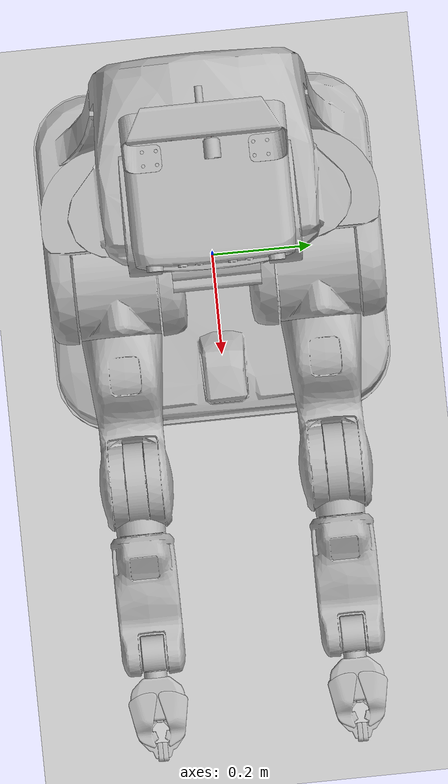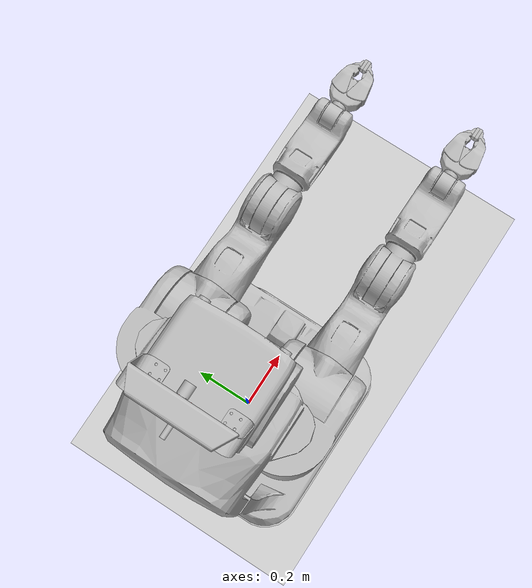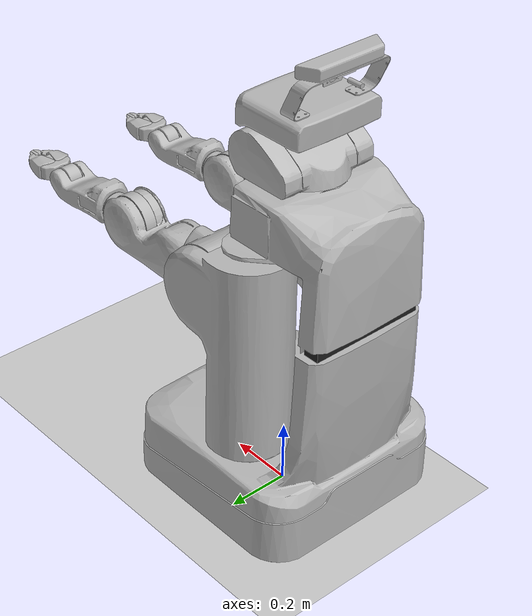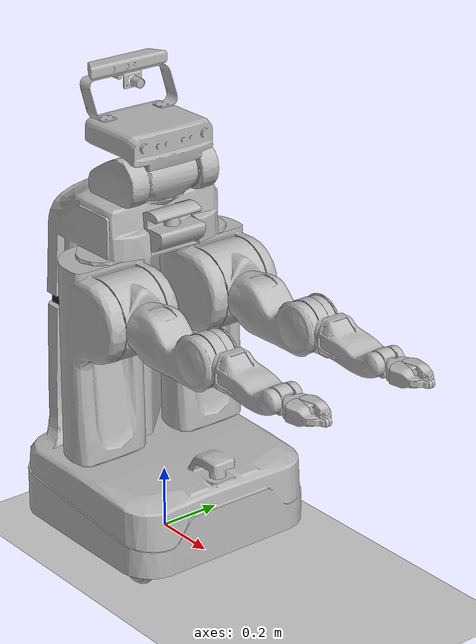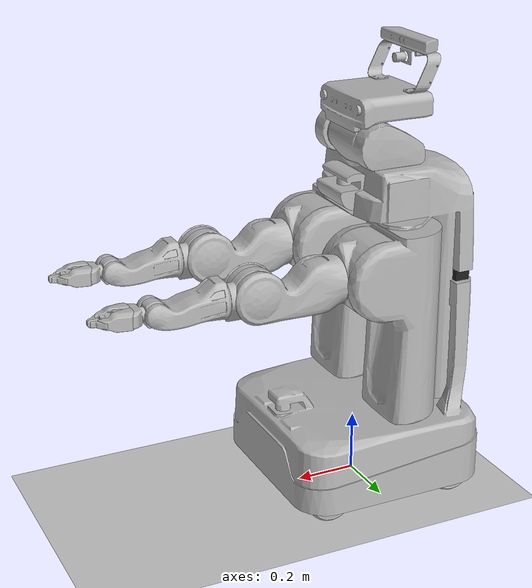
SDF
<sdf version="1.3">
 <world name="default">
  <light name="sun" type="directional">
   <pose>0.000000 0.000000 10.000000 0.000000 0.000000 0.000000</pose>
   <diffuse>0.800000 0.800000 0.800000 1.000000</diffuse>
   <specular>0.100000 0.100000 0.100000 1.000000</specular>
   <attenuation>
    <range>1000.000000</range>
    <constant>0.900000</constant>
    <linear>0.010000</linear>
    <quadratic>0.001000</quadratic>
   </attenuation>
   <direction>-0.500000 0.500000 -1.000000</direction>
  </light>
  <model name="ground_plane">
   <static>1</static>
   <link name="link">
    <collision name="collision">
     <geometry>
      <plane><normal>0.000000 0.000000 1.000000</normal><size>100.000000 100.000000</size></plane>
     </geometry>
     <surface><friction><ode><mu>100.000000</mu><mu2>50.000000</mu2></ode></friction></surface>
    </collision>
    <visual name="visual">
     <cast_shadows>0</cast_shadows>
     <geometry>
      <plane><normal>0.000000 0.000000 1.000000</normal><size>100.000000 100.000000</size></plane>
     </geometry>
     <material>
      <script><uri>file://media/materials/scripts/gazebo.material</uri><name>Gazebo/Grey</name></script>
     </material>
    </visual>
    <velocity_decay><linear>0.000000</linear><angular>0.000000</angular></velocity_decay>
   </link>
  </model>
  <physics type="ode">
   <update_rate>1000.000000</update_rate>
   <gravity>0.000000 0.000000 -9.800000</gravity>
  </physics>
  <scene>
   <ambient>0.200000 0.200000 0.200000 1.000000</ambient>
   <background>0.700000 0.700000 0.700000 1.000000</background>
   <shadows>1</shadows>
  </scene>
  <model name="pr2">
   <link name="base_footprint">
    <inertial>
     <pose>-0.062421 0.000000 0.201365 0.000000 0.000000 0.000000</pose>
     <mass>118.001000</mass>
     <inertia>
      <ixx>8.431730</ixx>
      <ixy>-0.009720</ixy>
      <ixz>1.901570</ixz>
      <iyy>8.533050</iyy>
      <iyz>-0.007380</iyz>
      <izz>3.787470</izz>
     </inertia>
    </inertial>
    <collision name="base_footprint_geom">
     <pose>0.000000 0.000000 0.071000 0.000000 0.000000 0.000000</pose>
     <geometry><box><size>0.001000 0.001000 0.001000</size></box></geometry>
    </collision>
    <collision name="base_footprint_geom_base_bellow_link">
     <pose>-0.290000 0.000000 0.851000 0.000000 0.000000 0.000000</pose>
     <geometry><box><size>0.050000 0.370000 0.300000</size></box></geometry>
    </collision>
    <collision name="base_footprint_geom_base_link">
     <pose>0.000000 0.000000 0.051000 0.000000 0.000000 0.000000</pose>
     <geometry>
      <mesh>
       <scale>1.000000 1.000000 1.000000</scale>
       <uri>/opt/ros/groovy/stacks/pr2_common/pr2_description/meshes/base_v0/base_L.stl</uri>
      </mesh>
     </geometry>
    </collision>
    <visual name="base_footprint_visual">
     <geometry><box><size>0.010000 0.010000 0.010000</size></box></geometry>
    </visual>
    <visual name="base_footprint_visualbase_bellow_link">
     <pose>-0.290000 0.000000 0.851000 0.000000 0.000000 0.000000</pose>
     <geometry><box><size>0.050000 0.370000 0.300000</size></box></geometry>
     <material><script><name>PR2/Black</name><uri>__default__</uri></script></material>
    </visual>
    <visual name="base_footprint_visualbase_link">
     <pose>0.000000 0.000000 0.051000 0.000000 0.000000 0.000000</pose>
     <geometry>
      <mesh>
       <scale>1.000000 1.000000 1.000000</scale>
       <uri>/opt/ros/groovy/stacks/pr2_common/pr2_description/meshes/base_v0/base.dae</uri>
      </mesh>
     </geometry>
    </visual>
    <velocity_decay><linear>0.000000</linear><angular>0.000000</angular></velocity_decay>
    <sensor name="base_contact_sensor" type="contact">
     <always_on>1</always_on>
     <update_rate>100.000000</update_rate>
     <contact><collision>base_footprint_geom_base_link</collision><topic>__default_topic__</topic></contact>
     <plugin name="base_gazebo_ros_bumper_controller" filename="libgazebo_ros_bumper.so">
      <alwaysOn>1</alwaysOn>
      <updateRate>100.0</updateRate>
      <bumperTopicName>base_bumper</bumperTopicName>
      <robotNamespace>/</robotNamespace>
     </plugin>
     <pose>0.000000 0.000000 0.051000 0.000000 0.000000 0.000000</pose>
    </sensor>
    <velocity_decay><linear>0.000000</linear><angular>0.000000</angular></velocity_decay>
    <velocity_decay><linear>0.000000</linear><angular>0.000000</angular></velocity_decay>
    <sensor name="base_laser" type="ray">
     <always_on>1</always_on>
     <update_rate>20.000000</update_rate>
     <visualize>0</visualize>
     <ray>
      <scan>
       <horizontal>
        <samples>640</samples>
        <resolution>1.000000</resolution>
        <min_angle>-2.268900</min_angle>
        <max_angle>2.268900</max_angle>
       </horizontal>
      </scan>
      <range><min>0.080000</min><max>10.000000</max><resolution>0.010000</resolution></range>
     </ray>
     <plugin name="gazebo_ros_base_laser_controller" filename="libgazebo_ros_laser.so">
      <gaussianNoise>0.005</gaussianNoise>
      <alwaysOn>1</alwaysOn>
      <updateRate>20</updateRate>
      <topicName>base_scan</topicName>
      <frameName>base_laser_link</frameName>
      <robotNamespace>/</robotNamespace>
     </plugin>
     <pose>0.275000 0.000000 0.303000 0.000000 0.000000 0.000000</pose>
    </sensor>
   </link>
   <link name="bl_caster_rotation_link">
    <pose>-0.224600 0.224600 0.079200 0.000000 0.000000 0.000000</pose>
    <inertial>
     <pose>0.000000 0.000000 0.070000 0.000000 0.000000 0.000000</pose>
     <mass>3.473080</mass>
     <inertia>
      <ixx>0.012412</ixx>
      <ixy>-0.000712</ixy>
      <ixz>0.000503</ixz>
      <iyy>0.015218</iyy>
      <iyz>-0.000004</iyz>
      <izz>0.011764</izz>
     </inertia>
    </inertial>
    <collision name="bl_caster_rotation_link_geom">
     <geometry>
      <mesh>
       <scale>1.000000 1.000000 1.000000</scale>
       <uri>/opt/ros/groovy/stacks/pr2_common/pr2_description/meshes/base_v0/caster_L.stl</uri>
      </mesh>
     </geometry>
    </collision>
    <visual name="bl_caster_rotation_link_visual">
     <geometry>
      <mesh>
       <scale>1.000000 1.000000 1.000000</scale>
       <uri>/opt/ros/groovy/stacks/pr2_common/pr2_description/meshes/base_v0/caster.stl</uri>
      </mesh>
     </geometry>
     <material><script><name>PR2/caster_texture</name><uri>__default__</uri></script></material>
    </visual>
    <velocity_decay><linear>0.000000</linear><angular>0.000000</angular></velocity_decay>
   </link>
   <joint name="bl_caster_rotation_joint" type="revolute">
    <child>bl_caster_rotation_link</child>
    <parent>base_footprint</parent>
    <axis>
     <xyz>0.000000 0.000000 1.000000</xyz>
     <limit><lower>-10000000000000000.000000</lower><upper>10000000000000000.000000</upper></limit>
     <dynamics><damping>1.000000</damping></dynamics>
    </axis>
   </joint>
   <link name="bl_caster_l_wheel_link">
    <pose>-0.224600 0.273600 0.079200 0.000000 0.000000 0.000000</pose>
    <inertial>
     <mass>0.440360</mass>
     <inertia>
      <ixx>0.012412</ixx>
      <ixy>-0.000712</ixy>
      <ixz>0.000503</ixz>
      <iyy>0.015218</iyy>
      <iyz>-0.000004</iyz>
      <izz>0.011764</izz>
     </inertia>
    </inertial>
    <collision name="bl_caster_l_wheel_link_geom">
     <pose>0.000000 0.000000 0.000000 1.570800 0.000000 0.000000</pose>
     <geometry><cylinder><length>0.034000</length><radius>0.074792</radius></cylinder></geometry>
     <surface>
      <contact>
       <ode>
        <kp>1000000.000000</kp>
        <kd>1.000000</kd>
        <max_vel>100.000000</max_vel>
        <min_depth>0.000000</min_depth>
       </ode>
      </contact>
      <friction><ode><mu>100.000000</mu><mu2>100.000000</mu2></ode></friction>
     </surface>
    </collision>
    <visual name="bl_caster_l_wheel_link_visual">
     <geometry>
      <mesh>
       <scale>1.000000 1.000000 1.000000</scale>
       <uri>/opt/ros/groovy/stacks/pr2_common/pr2_description/meshes/base_v0/wheel.dae</uri>
      </mesh>
     </geometry>
    </visual>
    <velocity_decay><linear>0.000000</linear><angular>0.000000</angular></velocity_decay>
   </link>
   <joint name="bl_caster_l_wheel_joint" type="revolute">
    <child>bl_caster_l_wheel_link</child>
    <parent>bl_caster_rotation_link</parent>
    <axis>
     <xyz>0.000000 1.000000 0.000000</xyz>
     <limit><lower>-10000000000000000.000000</lower><upper>10000000000000000.000000</upper></limit>
     <dynamics><damping>1.000000</damping></dynamics>
    </axis>
   </joint>
   <link name="bl_caster_r_wheel_link">
    <pose>-0.224600 0.175600 0.079200 0.000000 0.000000 0.000000</pose>
    <inertial>
     <mass>0.440360</mass>
     <inertia>
      <ixx>0.012412</ixx>
      <ixy>-0.000712</ixy>
      <ixz>0.000503</ixz>
      <iyy>0.015218</iyy>
      <iyz>-0.000004</iyz>
      <izz>0.011764</izz>
     </inertia>
    </inertial>
    <collision name="bl_caster_r_wheel_link_geom">
     <pose>0.000000 0.000000 0.000000 1.570800 0.000000 0.000000</pose>
     <geometry><cylinder><length>0.034000</length><radius>0.074792</radius></cylinder></geometry>
     <surface>
      <contact>
       <ode>
        <kp>1000000.000000</kp>
        <kd>1.000000</kd>
        <max_vel>100.000000</max_vel>
        <min_depth>0.000000</min_depth>
       </ode>
      </contact>
      <friction><ode><mu>100.000000</mu><mu2>100.000000</mu2></ode></friction>
     </surface>
    </collision>
    <visual name="bl_caster_r_wheel_link_visual">
     <geometry>
      <mesh>
       <scale>1.000000 1.000000 1.000000</scale>
       <uri>/opt/ros/groovy/stacks/pr2_common/pr2_description/meshes/base_v0/wheel.dae</uri>
      </mesh>
     </geometry>
    </visual>
    <velocity_decay><linear>0.000000</linear><angular>0.000000</angular></velocity_decay>
   </link>
   <joint name="bl_caster_r_wheel_joint" type="revolute">
    <child>bl_caster_r_wheel_link</child>
    <parent>bl_caster_rotation_link</parent>
    <axis>
     <xyz>0.000000 1.000000 0.000000</xyz>
     <limit><lower>-10000000000000000.000000</lower><upper>10000000000000000.000000</upper></limit>
     <dynamics><damping>1.000000</damping></dynamics>
    </axis>
   </joint>
   <link name="br_caster_rotation_link">
    <pose>-0.224600 -0.224600 0.079200 0.000000 0.000000 0.000000</pose>
    <inertial>
     <pose>0.000000 0.000000 0.070000 0.000000 0.000000 0.000000</pose>
     <mass>3.473080</mass>
     <inertia>
      <ixx>0.012412</ixx>
      <ixy>-0.000712</ixy>
      <ixz>0.000503</ixz>
      <iyy>0.015218</iyy>
      <iyz>-0.000004</iyz>
      <izz>0.011764</izz>
     </inertia>
    </inertial>
    <collision name="br_caster_rotation_link_geom">
     <geometry>
      <mesh>
       <scale>1.000000 1.000000 1.000000</scale>
       <uri>/opt/ros/groovy/stacks/pr2_common/pr2_description/meshes/base_v0/caster_L.stl</uri>
      </mesh>
     </geometry>
    </collision>
    <visual name="br_caster_rotation_link_visual">
     <geometry>
      <mesh>
       <scale>1.000000 1.000000 1.000000</scale>
       <uri>/opt/ros/groovy/stacks/pr2_common/pr2_description/meshes/base_v0/caster.stl</uri>
      </mesh>
     </geometry>
     <material><script><name>PR2/caster_texture</name><uri>__default__</uri></script></material>
    </visual>
    <velocity_decay><linear>0.000000</linear><angular>0.000000</angular></velocity_decay>
   </link>
   <joint name="br_caster_rotation_joint" type="revolute">
    <child>br_caster_rotation_link</child>
    <parent>base_footprint</parent>
    <axis>
     <xyz>0.000000 0.000000 1.000000</xyz>
     <limit><lower>-10000000000000000.000000</lower><upper>10000000000000000.000000</upper></limit>
     <dynamics><damping>1.000000</damping></dynamics>
    </axis>
   </joint>
   <link name="br_caster_l_wheel_link">
    <pose>-0.224600 -0.175600 0.079200 0.000000 0.000000 0.000000</pose>
    <inertial>
     <mass>0.440360</mass>
     <inertia>
      <ixx>0.012412</ixx>
      <ixy>-0.000712</ixy>
      <ixz>0.000503</ixz>
      <iyy>0.015218</iyy>
      <iyz>-0.000004</iyz>
      <izz>0.011764</izz>
     </inertia>
    </inertial>
    <collision name="br_caster_l_wheel_link_geom">
     <pose>0.000000 0.000000 0.000000 1.570800 0.000000 0.000000</pose>
     <geometry><cylinder><length>0.034000</length><radius>0.074792</radius></cylinder></geometry>
     <surface>
      <contact>
       <ode>
        <kp>1000000.000000</kp>
        <kd>1.000000</kd>
        <max_vel>100.000000</max_vel>
        <min_depth>0.000000</min_depth>
       </ode>
      </contact>
      <friction><ode><mu>100.000000</mu><mu2>100.000000</mu2></ode></friction>
     </surface>
    </collision>
    <visual name="br_caster_l_wheel_link_visual">
     <geometry>
      <mesh>
       <scale>1.000000 1.000000 1.000000</scale>
       <uri>/opt/ros/groovy/stacks/pr2_common/pr2_description/meshes/base_v0/wheel.dae</uri>
      </mesh>
     </geometry>
    </visual>
    <velocity_decay><linear>0.000000</linear><angular>0.000000</angular></velocity_decay>
   </link>
   <joint name="br_caster_l_wheel_joint" type="revolute">
    <child>br_caster_l_wheel_link</child>
    <parent>br_caster_rotation_link</parent>
    <axis>
     <xyz>0.000000 1.000000 0.000000</xyz>
     <limit><lower>-10000000000000000.000000</lower><upper>10000000000000000.000000</upper></limit>
     <dynamics><damping>1.000000</damping></dynamics>
    </axis>
   </joint>
   <link name="br_caster_r_wheel_link">
    <pose>-0.224600 -0.273600 0.079200 0.000000 0.000000 0.000000</pose>
    <inertial>
     <mass>0.440360</mass>
     <inertia>
      <ixx>0.012412</ixx>
      <ixy>-0.000712</ixy>
      <ixz>0.000503</ixz>
      <iyy>0.015218</iyy>
      <iyz>-0.000004</iyz>
      <izz>0.011764</izz>
     </inertia>
    </inertial>
    <collision name="br_caster_r_wheel_link_geom">
     <pose>0.000000 0.000000 0.000000 1.570800 0.000000 0.000000</pose>
     <geometry><cylinder><length>0.034000</length><radius>0.074792</radius></cylinder></geometry>
     <surface>
      <contact>
       <ode>
        <kp>1000000.000000</kp>
        <kd>1.000000</kd>
        <max_vel>100.000000</max_vel>
        <min_depth>0.000000</min_depth>
       </ode>
      </contact>
      <friction><ode><mu>100.000000</mu><mu2>100.000000</mu2></ode></friction>
     </surface>
    </collision>
    <visual name="br_caster_r_wheel_link_visual">
     <geometry>
      <mesh>
       <scale>1.000000 1.000000 1.000000</scale>
       <uri>/opt/ros/groovy/stacks/pr2_common/pr2_description/meshes/base_v0/wheel.dae</uri>
      </mesh>
     </geometry>
    </visual>
    <velocity_decay><linear>0.000000</linear><angular>0.000000</angular></velocity_decay>
   </link>
   <joint name="br_caster_r_wheel_joint" type="revolute">
    <child>br_caster_r_wheel_link</child>
    <parent>br_caster_rotation_link</parent>
    <axis>
     <xyz>0.000000 1.000000 0.000000</xyz>
     <limit><lower>-10000000000000000.000000</lower><upper>10000000000000000.000000</upper></limit>
     <dynamics><damping>1.000000</damping></dynamics>
    </axis>
   </joint>
   <link name="fl_caster_rotation_link">
    <pose>0.224600 0.224600 0.079200 0.000000 0.000000 0.000000</pose>
    <inertial>
     <pose>0.000000 0.000000 0.070000 0.000000 0.000000 0.000000</pose>
     <mass>3.473080</mass>
     <inertia>
      <ixx>0.012412</ixx>
      <ixy>-0.000712</ixy>
      <ixz>0.000503</ixz>
      <iyy>0.015218</iyy>
      <iyz>-0.000004</iyz>
      <izz>0.011764</izz>
     </inertia>
    </inertial>
    <collision name="fl_caster_rotation_link_geom">
     <geometry>
      <mesh>
       <scale>1.000000 1.000000 1.000000</scale>
       <uri>/opt/ros/groovy/stacks/pr2_common/pr2_description/meshes/base_v0/caster_L.stl</uri>
      </mesh>
     </geometry>
    </collision>
    <visual name="fl_caster_rotation_link_visual">
     <geometry>
      <mesh>
       <scale>1.000000 1.000000 1.000000</scale>
       <uri>/opt/ros/groovy/stacks/pr2_common/pr2_description/meshes/base_v0/caster.stl</uri>
      </mesh>
     </geometry>
     <material><script><name>PR2/caster_texture</name><uri>__default__</uri></script></material>
    </visual>
    <velocity_decay><linear>0.000000</linear><angular>0.000000</angular></velocity_decay>
   </link>
   <joint name="fl_caster_rotation_joint" type="revolute">
    <child>fl_caster_rotation_link</child>
    <parent>base_footprint</parent>
    <axis>
     <xyz>0.000000 0.000000 1.000000</xyz>
     <limit><lower>-10000000000000000.000000</lower><upper>10000000000000000.000000</upper></limit>
     <dynamics><damping>1.000000</damping></dynamics>
    </axis>
   </joint>
   <link name="fl_caster_l_wheel_link">
    <pose>0.224600 0.273600 0.079200 0.000000 0.000000 0.000000</pose>
    <inertial>
     <mass>0.440360</mass>
     <inertia>
      <ixx>0.012412</ixx>
      <ixy>-0.000712</ixy>
      <ixz>0.000503</ixz>
      <iyy>0.015218</iyy>
      <iyz>-0.000004</iyz>
      <izz>0.011764</izz>
     </inertia>
    </inertial>
    <collision name="fl_caster_l_wheel_link_geom">
     <pose>0.000000 0.000000 0.000000 1.570800 0.000000 0.000000</pose>
     <geometry><cylinder><length>0.034000</length><radius>0.074792</radius></cylinder></geometry>
     <surface>
      <contact>
       <ode>
        <kp>1000000.000000</kp>
        <kd>1.000000</kd>
        <max_vel>100.000000</max_vel>
        <min_depth>0.000000</min_depth>
       </ode>
      </contact>
      <friction><ode><mu>100.000000</mu><mu2>100.000000</mu2></ode></friction>
     </surface>
    </collision>
    <visual name="fl_caster_l_wheel_link_visual">
     <geometry>
      <mesh>
       <scale>1.000000 1.000000 1.000000</scale>
       <uri>/opt/ros/groovy/stacks/pr2_common/pr2_description/meshes/base_v0/wheel.dae</uri>
      </mesh>
     </geometry>
    </visual>
    <velocity_decay><linear>0.000000</linear><angular>0.000000</angular></velocity_decay>
   </link>
   <joint name="fl_caster_l_wheel_joint" type="revolute">
    <child>fl_caster_l_wheel_link</child>
    <parent>fl_caster_rotation_link</parent>
    <axis>
     <xyz>0.000000 1.000000 0.000000</xyz>
     <limit><lower>-10000000000000000.000000</lower><upper>10000000000000000.000000</upper></limit>
     <dynamics><damping>1.000000</damping></dynamics>
    </axis>
   </joint>
   <link name="fl_caster_r_wheel_link">
    <pose>0.224600 0.175600 0.079200 0.000000 0.000000 0.000000</pose>
    <inertial>
     <mass>0.440360</mass>
     <inertia>
      <ixx>0.012412</ixx>
      <ixy>-0.000712</ixy>
      <ixz>0.000503</ixz>
      <iyy>0.015218</iyy>
      <iyz>-0.000004</iyz>
      <izz>0.011764</izz>
     </inertia>
    </inertial>
    <collision name="fl_caster_r_wheel_link_geom">
     <pose>0.000000 0.000000 0.000000 1.570800 0.000000 0.000000</pose>
     <geometry><cylinder><length>0.034000</length><radius>0.074792</radius></cylinder></geometry>
     <surface>
      <contact>
       <ode>
        <kp>1000000.000000</kp>
        <kd>1.000000</kd>
        <max_vel>100.000000</max_vel>
        <min_depth>0.000000</min_depth>
       </ode>
      </contact>
      <friction><ode><mu>100.000000</mu><mu2>100.000000</mu2></ode></friction>
     </surface>
    </collision>
    <visual name="fl_caster_r_wheel_link_visual">
     <geometry>
      <mesh>
       <scale>1.000000 1.000000 1.000000</scale>
       <uri>/opt/ros/groovy/stacks/pr2_common/pr2_description/meshes/base_v0/wheel.dae</uri>
      </mesh>
     </geometry>
    </visual>
    <velocity_decay><linear>0.000000</linear><angular>0.000000</angular></velocity_decay>
   </link>
   <joint name="fl_caster_r_wheel_joint" type="revolute">
    <child>fl_caster_r_wheel_link</child>
    <parent>fl_caster_rotation_link</parent>
    <axis>
     <xyz>0.000000 1.000000 0.000000</xyz>
     <limit><lower>-10000000000000000.000000</lower><upper>10000000000000000.000000</upper></limit>
     <dynamics><damping>1.000000</damping></dynamics>
    </axis>
   </joint>
   <link name="fr_caster_rotation_link">
    <pose>0.224600 -0.224600 0.079200 0.000000 0.000000 0.000000</pose>
    <inertial>
     <pose>0.000000 0.000000 0.070000 0.000000 0.000000 0.000000</pose>
     <mass>3.473080</mass>
     <inertia>
      <ixx>0.012412</ixx>
      <ixy>-0.000712</ixy>
      <ixz>0.000503</ixz>
      <iyy>0.015218</iyy>
      <iyz>-0.000004</iyz>
      <izz>0.011764</izz>
     </inertia>
    </inertial>
    <collision name="fr_caster_rotation_link_geom">
     <geometry>
      <mesh>
       <scale>1.000000 1.000000 1.000000</scale>
       <uri>/opt/ros/groovy/stacks/pr2_common/pr2_description/meshes/base_v0/caster_L.stl</uri>
      </mesh>
     </geometry>
    </collision>
    <visual name="fr_caster_rotation_link_visual">
     <geometry>
      <mesh>
       <scale>1.000000 1.000000 1.000000</scale>
       <uri>/opt/ros/groovy/stacks/pr2_common/pr2_description/meshes/base_v0/caster.stl</uri>
      </mesh>
     </geometry>
     <material><script><name>PR2/caster_texture</name><uri>__default__</uri></script></material>
    </visual>
    <velocity_decay><linear>0.000000</linear><angular>0.000000</angular></velocity_decay>
   </link>
   <joint name="fr_caster_rotation_joint" type="revolute">
    <child>fr_caster_rotation_link</child>
    <parent>base_footprint</parent>
    <axis>
     <xyz>0.000000 0.000000 1.000000</xyz>
     <limit><lower>-10000000000000000.000000</lower><upper>10000000000000000.000000</upper></limit>
     <dynamics><damping>1.000000</damping></dynamics>
    </axis>
   </joint>
   <link name="fr_caster_l_wheel_link">
    <pose>0.224600 -0.175600 0.079200 0.000000 0.000000 0.000000</pose>
    <inertial>
     <mass>0.440360</mass>
     <inertia>
      <ixx>0.012412</ixx>
      <ixy>-0.000712</ixy>
      <ixz>0.000503</ixz>
      <iyy>0.015218</iyy>
      <iyz>-0.000004</iyz>
      <izz>0.011764</izz>
     </inertia>
    </inertial>
    <collision name="fr_caster_l_wheel_link_geom">
     <pose>0.000000 0.000000 0.000000 1.570800 0.000000 0.000000</pose>
     <geometry><cylinder><length>0.034000</length><radius>0.074792</radius></cylinder></geometry>
     <surface>
      <contact>
       <ode>
        <kp>1000000.000000</kp>
        <kd>1.000000</kd>
        <max_vel>100.000000</max_vel>
        <min_depth>0.000000</min_depth>
       </ode>
      </contact>
      <friction><ode><mu>100.000000</mu><mu2>100.000000</mu2></ode></friction>
     </surface>
    </collision>
    <visual name="fr_caster_l_wheel_link_visual">
     <geometry>
      <mesh>
       <scale>1.000000 1.000000 1.000000</scale>
       <uri>/opt/ros/groovy/stacks/pr2_common/pr2_description/meshes/base_v0/wheel.dae</uri>
      </mesh>
     </geometry>
    </visual>
    <velocity_decay><linear>0.000000</linear><angular>0.000000</angular></velocity_decay>
   </link>
   <joint name="fr_caster_l_wheel_joint" type="revolute">
    <child>fr_caster_l_wheel_link</child>
    <parent>fr_caster_rotation_link</parent>
    <axis>
     <xyz>0.000000 1.000000 0.000000</xyz>
     <limit><lower>-10000000000000000.000000</lower><upper>10000000000000000.000000</upper></limit>
     <dynamics><damping>1.000000</damping></dynamics>
    </axis>
   </joint>
   <link name="fr_caster_r_wheel_link">
    <pose>0.224600 -0.273600 0.079200 0.000000 0.000000 0.000000</pose>
    <inertial>
     <mass>0.440360</mass>
     <inertia>
      <ixx>0.012412</ixx>
      <ixy>-0.000712</ixy>
      <ixz>0.000503</ixz>
      <iyy>0.015218</iyy>
      <iyz>-0.000004</iyz>
      <izz>0.011764</izz>
     </inertia>
    </inertial>
    <collision name="fr_caster_r_wheel_link_geom">
     <pose>0.000000 0.000000 0.000000 1.570800 0.000000 0.000000</pose>
     <geometry><cylinder><length>0.034000</length><radius>0.074792</radius></cylinder></geometry>
     <surface>
      <contact>
       <ode>
        <kp>1000000.000000</kp>
        <kd>1.000000</kd>
        <max_vel>100.000000</max_vel>
        <min_depth>0.000000</min_depth>
       </ode>
      </contact>
      <friction><ode><mu>100.000000</mu><mu2>100.000000</mu2></ode></friction>
     </surface>
    </collision>
    <visual name="fr_caster_r_wheel_link_visual">
     <geometry>
      <mesh>
       <scale>1.000000 1.000000 1.000000</scale>
       <uri>/opt/ros/groovy/stacks/pr2_common/pr2_description/meshes/base_v0/wheel.dae</uri>
      </mesh>
     </geometry>
    </visual>
    <velocity_decay><linear>0.000000</linear><angular>0.000000</angular></velocity_decay>
   </link>
   <joint name="fr_caster_r_wheel_joint" type="revolute">
    <child>fr_caster_r_wheel_link</child>
    <parent>fr_caster_rotation_link</parent>
    <axis>
     <xyz>0.000000 1.000000 0.000000</xyz>
     <limit><lower>-10000000000000000.000000</lower><upper>10000000000000000.000000</upper></limit>
     <dynamics><damping>1.000000</damping></dynamics>
    </axis>
   </joint>
   <link name="torso_lift_link">
    <pose>-0.050000 0.000000 0.790675 0.000000 0.000000 0.000000</pose>
    <inertial>
     <pose>-0.099499 -0.000004 -0.086764 0.000000 0.000000 0.000000</pose>
     <mass>36.449000</mass>
     <inertia>
      <ixx>2.792330</ixx>
      <ixy>0.004280</ixy>
      <ixz>-0.160631</ixz>
      <iyy>2.521060</iyy>
      <iyz>0.029689</iyz>
      <izz>0.536551</izz>
     </inertia>
    </inertial>
    <collision name="torso_lift_link_geom">
     <geometry>
      <mesh>
       <scale>1.000000 1.000000 1.000000</scale>
       <uri>/opt/ros/groovy/stacks/pr2_common/pr2_description/meshes/torso_v0/torso_lift_L.stl</uri>
      </mesh>
     </geometry>
    </collision>
    <visual name="torso_lift_link_visual">
     <geometry>
      <mesh>
       <scale>1.000000 1.000000 1.000000</scale>
       <uri>/opt/ros/groovy/stacks/pr2_common/pr2_description/meshes/torso_v0/torso_lift.dae</uri>
      </mesh>
     </geometry>
    </visual>
    <velocity_decay><linear>0.000000</linear><angular>0.000000</angular></velocity_decay>
    <sensor name="torso_lift_contact_sensor" type="contact">
     <contact><collision>torso_lift_link_geom</collision><topic>__default_topic__</topic></contact>
     <update_rate>100.000000</update_rate>
     <plugin name="torso_lift_gazebo_ros_bumper_controller" filename="libgazebo_ros_bumper.so">
      <alwaysOn>1</alwaysOn>
      <updateRate>100.0</updateRate>
      <bumperTopicName>torso_lift_bumper</bumperTopicName>
      <robotNamespace>/</robotNamespace>
     </plugin>
    </sensor>
   </link>
   <joint name="torso_lift_joint" type="prismatic">
    <child>torso_lift_link</child>
    <parent>base_footprint</parent>
    <axis>
     <xyz>0.000000 0.000000 1.000000</xyz>
     <limit>
      <lower>0.000000</lower>
      <upper>0.330000</upper>
      <effort>10000.000000</effort>
      <velocity>0.013000</velocity>
     </limit>
     <dynamics><damping>20000.000000</damping></dynamics>
    </axis>
   </joint>
   <link name="head_pan_link">
    <pose>-0.067070 0.000000 1.172130 0.000000 0.000000 0.000000</pose>
    <inertial>
     <pose>0.010907 0.031693 0.090507 0.000000 0.000000 0.000000</pose>
     <mass>6.339000</mass>
     <inertia>
      <ixx>0.032498</ixx>
      <ixy>0.000636</ixy>
      <ixz>0.002585</ixz>
      <iyy>0.046546</iyy>
      <iyz>-0.002453</iyz>
      <izz>0.057653</izz>
     </inertia>
    </inertial>
    <collision name="head_pan_link_geom">
     <geometry>
      <mesh>
       <scale>1.000000 1.000000 1.000000</scale>
       <uri>/opt/ros/groovy/stacks/pr2_common/pr2_description/meshes/head_v0/head_pan_L.stl</uri>
      </mesh>
     </geometry>
    </collision>
    <visual name="head_pan_link_visual">
     <geometry>
      <mesh>
       <scale>1.000000 1.000000 1.000000</scale>
       <uri>/opt/ros/groovy/stacks/pr2_common/pr2_description/meshes/head_v0/head_pan.dae</uri>
      </mesh>
     </geometry>
    </visual>
    <velocity_decay><linear>0.000000</linear><angular>0.000000</angular></velocity_decay>
   </link>
   <joint name="head_pan_joint" type="revolute">
    <child>head_pan_link</child>
    <parent>torso_lift_link</parent>
    <axis>
     <xyz>0.000000 0.000000 1.000000</xyz>
     <limit>
      <lower>-3.007000</lower>
      <upper>3.007000</upper>
      <effort>2.645000</effort>
      <velocity>6.000000</velocity>
     </limit>
     <dynamics><damping>0.500000</damping></dynamics>
    </axis>
   </joint>
   <link name="head_tilt_link">
    <pose>0.000930 0.000000 1.172130 0.000000 0.000000 0.000000</pose>
    <inertial>
     <pose>-0.005151 -0.014635 0.072819 0.000000 0.000000 0.000000</pose>
     <mass>5.319000</mass>
     <inertia>
      <ixx>0.126134</ixx>
      <ixy>0.000237</ixy>
      <ixz>0.011881</ixz>
      <iyy>0.165102</iyy>
      <iyz>0.001606</iyz>
      <izz>0.166947</izz>
     </inertia>
    </inertial>
    <collision name="head_tilt_link_geom">
     <geometry>
      <mesh>
       <scale>1.000000 1.000000 1.000000</scale>
       <uri>/opt/ros/groovy/stacks/pr2_common/pr2_description/meshes/head_v0/head_tilt_L.stl</uri>
      </mesh>
     </geometry>
    </collision>
    <collision name="head_tilt_link_geom_head_mount_kinect_ir_link">
     <pose>-0.147067 0.012500 0.291953 0.000000 0.000000 0.000000</pose>
     <geometry><sphere><radius>0.000500</radius></sphere></geometry>
    </collision>
    <collision name="head_tilt_link_geom_head_mount_kinect_rgb_link">
     <pose>-0.147067 -0.017500 0.291953 0.000000 0.000000 0.000000</pose>
     <geometry><sphere><radius>0.000500</radius></sphere></geometry>
    </collision>
    <collision name="head_tilt_link_geom_head_mount_link">
     <pose>-0.114800 0.000000 0.155500 0.000000 0.000000 0.000000</pose>
     <geometry><sphere><radius>0.000500</radius></sphere></geometry>
    </collision>
    <collision name="head_tilt_link_geom_head_mount_prosilica_link">
     <pose>-0.161257 0.012500 0.244421 0.000000 0.000000 0.000000</pose>
     <geometry><sphere><radius>0.000500</radius></sphere></geometry>
    </collision>
    <collision name="head_tilt_link_geom_head_plate_frame">
     <pose>0.023200 0.000000 0.064500 0.000000 0.000000 0.000000</pose>
     <geometry><box><size>0.010000 0.010000 0.010000</size></box></geometry>
    </collision>
    <visual name="head_tilt_link_visual">
     <geometry>
      <mesh>
       <scale>1.000000 1.000000 1.000000</scale>
       <uri>/opt/ros/groovy/stacks/pr2_common/pr2_description/meshes/head_v0/head_tilt.dae</uri>
      </mesh>
     </geometry>
    </visual>
    <visual name="head_tilt_link_visualdouble_stereo_link">
     <pose>0.013200 0.000000 0.089500 0.000000 0.000000 0.000000</pose>
     <geometry><box><size>0.020000 0.120000 0.050000</size></box></geometry>
    </visual>
    <visual name="head_tilt_link_visualhead_mount_kinect_ir_link">
     <pose>-0.147067 0.012500 0.291953 0.000000 0.000000 0.000000</pose>
     <geometry><sphere><radius>0.000500</radius></sphere></geometry>
     <material><script><name>Gazebo/Red</name><uri>__default__</uri></script></material>
    </visual>
    <visual name="head_tilt_link_visualhead_mount_kinect_rgb_link">
     <pose>-0.147067 -0.017500 0.291953 0.000000 0.000000 0.000000</pose>
     <geometry><sphere><radius>0.000500</radius></sphere></geometry>
     <material><script><name>Gazebo/Red</name><uri>__default__</uri></script></material>
    </visual>
    <visual name="head_tilt_link_visualhead_mount_link">
     <pose>-0.114800 0.000000 0.155500 0.000000 0.000000 0.000000</pose>
     <geometry>
      <mesh>
       <scale>0.001000 0.001000 0.001000</scale>
       <uri>/opt/ros/groovy/stacks/pr2_common/pr2_description/meshes/sensors/kinect_prosilica_v0/115x100_swept_back--coarse.STL</uri>
      </mesh>
     </geometry>
    </visual>
    <visual name="head_tilt_link_visualhead_mount_prosilica_link">
     <pose>-0.161257 0.012500 0.244421 0.000000 0.000000 0.000000</pose>
     <geometry><sphere><radius>0.000500</radius></sphere></geometry>
     <material><script><name>Gazebo/Red</name><uri>__default__</uri></script></material>
    </visual>
    <visual name="head_tilt_link_visualhead_plate_frame">
     <pose>0.023200 0.000000 0.064500 0.000000 0.000000 0.000000</pose>
     <geometry><box><size>0.010000 0.010000 0.010000</size></box></geometry>
     <material><script><name>Gazebo/Grey</name><uri>__default__</uri></script></material>
    </visual>
    <visual name="head_tilt_link_visualsensor_mount_link">
     <pose>0.023200 0.000000 0.064500 0.000000 0.000000 0.000000</pose>
     <geometry><box><size>0.010000 0.010000 0.010000</size></box></geometry>
    </visual>
    <velocity_decay><linear>0.000000</linear><angular>0.000000</angular></velocity_decay>
    <velocity_decay><linear>0.000000</linear><angular>0.000000</angular></velocity_decay>
    <sensor name="head_mount_ir_sensor" type="depth">
     <always_on>1</always_on>
     <update_rate>1.000000</update_rate>
     <camera name="__default__">
      <horizontal_fov>0.994838</horizontal_fov>
      <image><format>L8</format><width>640</width><height>480</height></image>
      <clip><near>0.010000</near><far>5.000000</far></clip>
     </camera>
     <plugin name="head_mount_kinect_ir_link_controller" filename="libgazebo_ros_openni_kinect.so">
      <baseline>0.2</baseline>
      <alwaysOn>1</alwaysOn>
      <updateRate>1.0</updateRate>
      <cameraName>head_mount_kinect_ir</cameraName>
      <imageTopicName>/head_mount_kinect/depth/image_raw</imageTopicName>
      <cameraInfoTopicName>/head_mount_kinect/depth/camera_info</cameraInfoTopicName>
      <depthImageTopicName>/head_mount_kinect/depth/image_raw</depthImageTopicName>
      <depthImageInfoTopicName>/head_mount_kinect/depth/camera_info</depthImageInfoTopicName>
      <pointCloudTopicName>/head_mount_kinect/depth/points</pointCloudTopicName>
      <frameName>head_mount_kinect_ir_optical_frame</frameName>
      <pointCloudCutoff>0.5</pointCloudCutoff>
      <distortionK1>0.00000001</distortionK1>
      <distortionK2>0.00000001</distortionK2>
      <distortionK3>0.00000001</distortionK3>
      <distortionT1>0.00000001</distortionT1>
      <distortionT2>0.00000001</distortionT2>
      <robotNamespace>/</robotNamespace>
     </plugin>
     <pose>-0.147067 0.012500 0.291953 0.000000 0.000000 0.000000</pose>
    </sensor>
    <velocity_decay><linear>0.000000</linear><angular>0.000000</angular></velocity_decay>
    <sensor name="head_mount_rgb_sensor" type="depth">
     <always_on>1</always_on>
     <update_rate>1.000000</update_rate>
     <camera name="__default__">
      <horizontal_fov>0.994838</horizontal_fov>
      <image><format>R8G8B8</format><width>640</width><height>480</height></image>
      <clip><near>0.010000</near><far>5.000000</far></clip>
     </camera>
     <plugin name="head_mount_kinect_rgb_link_controller" filename="libgazebo_ros_openni_kinect.so">
      <alwaysOn>1</alwaysOn>
      <updateRate>1.0</updateRate>
      <cameraName>head_mount_kinect_rgb</cameraName>
      <imageTopicName>/head_mount_kinect/rgb/image_raw</imageTopicName>
      <cameraInfoTopicName>/head_mount_kinect/rgb/camera_info</cameraInfoTopicName>
      <pointCloudTopicName>/head_mount_kinect/depth_registered/points</pointCloudTopicName>
      <frameName>head_mount_kinect_rgb_optical_frame</frameName>
      <pointCloudCutoff>0.5</pointCloudCutoff>
      <distortionK1>0.00000001</distortionK1>
      <distortionK2>0.00000001</distortionK2>
      <distortionK3>0.00000001</distortionK3>
      <distortionT1>0.00000001</distortionT1>
      <distortionT2>0.00000001</distortionT2>
      <robotNamespace>/</robotNamespace>
     </plugin>
     <pose>-0.147067 -0.017500 0.291953 0.000000 0.000000 0.000000</pose>
    </sensor>
    <velocity_decay><linear>0.000000</linear><angular>0.000000</angular></velocity_decay>
    <sensor name="head_mount_prosilica_link_sensor" type="depth">
     <always_on>1</always_on>
     <update_rate>1.000000</update_rate>
     <camera name="__default__">
      <horizontal_fov>1.120501</horizontal_fov>
      <image><format>R8G8B8</format><width>320</width><height>240</height></image>
      <clip><near>0.100000</near><far>100.000000</far></clip>
     </camera>
     <plugin name="head_mount_prosilica_link_controller" filename="libgazebo_ros_prosilica.so">
      <alwaysOn>1</alwaysOn>
      <updateRate>1.0</updateRate>
      <cameraName>prosilica_camera_1mb</cameraName>
      <imageTopicName>image_raw</imageTopicName>
      <cameraInfoTopicName>camera_info</cameraInfoTopicName>
      <pollServiceName>request_image</pollServiceName>
      <frameName>head_mount_prosilica_optical_frame</frameName>
      <distortionK1>0.0</distortionK1>
      <distortionK2>0.0</distortionK2>
      <distortionK3>0.0</distortionK3>
      <distortionT1>0.0</distortionT1>
      <distortionT2>0.0</distortionT2>
      <robotNamespace>/</robotNamespace>
     </plugin>
     <pose>-0.161257 0.012500 0.244421 0.000000 0.000000 0.000000</pose>
    </sensor>
    <sensor name="head_mount_prosilica_link_sim_pcd_sensor" type="depth">
     <always_on>1</always_on>
     <update_rate>1.000000</update_rate>
     <camera name="__default__">
      <horizontal_fov>1.120501</horizontal_fov>
      <image><format>R8G8B8</format><width>320</width><height>240</height></image>
      <clip><near>0.100000</near><far>100.000000</far></clip>
     </camera>
     <plugin name="head_mount_prosilica_link_sim_pcd_controller" filename="libgazebo_ros_openni_kinect.so">
      <alwaysOn>1</alwaysOn>
      <updateRate>1.0</updateRate>
      <cameraName>prosilica_camera_1mb_sim_pcd</cameraName>
      <imageTopicName>image_raw</imageTopicName>
      <cameraInfoTopicName>camera_info</cameraInfoTopicName>
      <frameName>head_mount_prosilica_optical_frame</frameName>
      <robotNamespace>/</robotNamespace>
     </plugin>
     <pose>-0.161257 0.012500 0.244421 0.000000 0.000000 0.000000</pose>
    </sensor>
    <velocity_decay><linear>0.000000</linear><angular>0.000000</angular></velocity_decay>
    <projector name="projector_wg6802418_projector_wg6802418">
     <texture>stereo_projection_pattern_high_res_red.png</texture>
     <fov>0.959931</fov>
     <near_clip>0.100000</near_clip>
     <far_clip>10.000000</far_clip>
     <pose>0.023200 0.110000 0.119100 -3.141592 -1.570793 -3.141592</pose>
    </projector>
    <velocity_decay><linear>0.000000</linear><angular>0.000000</angular></velocity_decay>
    <velocity_decay><linear>0.000000</linear><angular>0.000000</angular></velocity_decay>
    <sensor name="narrow_stereo_l_stereo_camera_sensor" type="depth">
     <always_on>1</always_on>
     <update_rate>25.000000</update_rate>
     <camera name="__default__">
      <horizontal_fov>0.785398</horizontal_fov>
      <image><format>L8</format><width>640</width><height>480</height></image>
      <clip><near>0.100000</near><far>100.000000</far></clip>
     </camera>
     <plugin name="narrow_stereo_l_stereo_camera_controller" filename="libgazebo_ros_depth_camera.so">
      <alwaysOn>1</alwaysOn>
      <updateRate>25.0</updateRate>
      <cameraName>narrow_stereo/left</cameraName>
      <imageTopicName>image_raw</imageTopicName>
      <cameraInfoTopicName>camera_info</cameraInfoTopicName>
      <frameName>narrow_stereo_optical_frame</frameName>
      <hackBaseline>0</hackBaseline>
      <CxPrime>320.5</CxPrime>
      <Cx>320.5</Cx>
      <Cy>240.5</Cy>
      <focalLength>772.55</focalLength>
      <distortionK1>0.0</distortionK1>
      <distortionK2>0.0</distortionK2>
      <distortionK3>0.0</distortionK3>
      <distortionT1>0.0</distortionT1>
      <distortionT2>0.0</distortionT2>
      <robotNamespace>/</robotNamespace>
     </plugin>
     <pose>0.068200 0.060000 0.114600 0.000000 0.000000 0.000000</pose>
    </sensor>
    <velocity_decay><linear>0.000000</linear><angular>0.000000</angular></velocity_decay>
    <sensor name="narrow_stereo_r_stereo_camera_sensor" type="depth">
     <always_on>1</always_on>
     <update_rate>25.000000</update_rate>
     <camera name="__default__">
      <horizontal_fov>0.785398</horizontal_fov>
      <image><format>L8</format><width>640</width><height>480</height></image>
      <clip><near>0.100000</near><far>100.000000</far></clip>
     </camera>
     <plugin name="narrow_stereo_r_stereo_camera_controller" filename="libgazebo_ros_depth_camera.so">
      <alwaysOn>1</alwaysOn>
      <updateRate>25.0</updateRate>
      <cameraName>narrow_stereo/right</cameraName>
      <imageTopicName>image_raw</imageTopicName>
      <cameraInfoTopicName>camera_info</cameraInfoTopicName>
      <frameName>narrow_stereo_optical_frame</frameName>
      <hackBaseline>0.09</hackBaseline>
      <CxPrime>320.5</CxPrime>
      <Cx>320.5</Cx>
      <Cy>240.5</Cy>
      <focalLength>772.55</focalLength>
      <distortionK1>0.0</distortionK1>
      <distortionK2>0.0</distortionK2>
      <distortionK3>0.0</distortionK3>
      <distortionT1>0.0</distortionT1>
      <distortionT2>0.0</distortionT2>
      <robotNamespace>/</robotNamespace>
     </plugin>
     <pose>0.068200 -0.030000 0.114600 0.000000 0.000000 0.000000</pose>
    </sensor>
    <velocity_decay><linear>0.000000</linear><angular>0.000000</angular></velocity_decay>
    <velocity_decay><linear>0.000000</linear><angular>0.000000</angular></velocity_decay>
    <velocity_decay><linear>0.000000</linear><angular>0.000000</angular></velocity_decay>
    <sensor name="wide_stereo_l_stereo_camera_sensor" type="depth">
     <always_on>1</always_on>
     <update_rate>25.000000</update_rate>
     <camera name="__default__">
      <horizontal_fov>1.570796</horizontal_fov>
      <image><format>BAYER_BGGR8</format><width>640</width><height>480</height></image>
      <clip><near>0.100000</near><far>100.000000</far></clip>
     </camera>
     <plugin name="wide_stereo_l_stereo_camera_controller" filename="libgazebo_ros_depth_camera.so">
      <alwaysOn>1</alwaysOn>
      <updateRate>25.0</updateRate>
      <cameraName>wide_stereo/left</cameraName>
      <imageTopicName>image_raw</imageTopicName>
      <cameraInfoTopicName>camera_info</cameraInfoTopicName>
      <frameName>wide_stereo_optical_frame</frameName>
      <hackBaseline>0</hackBaseline>
      <CxPrime>320.5</CxPrime>
      <Cx>320.5</Cx>
      <Cy>240.5</Cy>
      <focalLength>320</focalLength>
      <distortionK1>0.0</distortionK1>
      <distortionK2>0.0</distortionK2>
      <distortionK3>0.0</distortionK3>
      <distortionT1>0.0</distortionT1>
      <distortionT2>0.0</distortionT2>
      <robotNamespace>/</robotNamespace>
     </plugin>
     <pose>0.068200 0.030000 0.114600 0.000000 0.000000 0.000000</pose>
    </sensor>
    <velocity_decay><linear>0.000000</linear><angular>0.000000</angular></velocity_decay>
    <sensor name="wide_stereo_r_stereo_camera_sensor" type="depth">
     <always_on>1</always_on>
     <update_rate>25.000000</update_rate>
     <camera name="__default__">
      <horizontal_fov>1.570796</horizontal_fov>
      <image><format>BAYER_BGGR8</format><width>640</width><height>480</height></image>
      <clip><near>0.100000</near><far>100.000000</far></clip>
     </camera>
     <plugin name="wide_stereo_r_stereo_camera_controller" filename="libgazebo_ros_depth_camera.so">
      <alwaysOn>1</alwaysOn>
      <updateRate>25.0</updateRate>
      <cameraName>wide_stereo/right</cameraName>
      <imageTopicName>image_raw</imageTopicName>
      <cameraInfoTopicName>camera_info</cameraInfoTopicName>
      <frameName>wide_stereo_optical_frame</frameName>
      <hackBaseline>0.09</hackBaseline>
      <CxPrime>320.5</CxPrime>
      <Cx>320.5</Cx>
      <Cy>240.5</Cy>
      <focalLength>320</focalLength>
      <distortionK1>0.0</distortionK1>
      <distortionK2>0.0</distortionK2>
      <distortionK3>0.0</distortionK3>
      <distortionT1>0.0</distortionT1>
      <distortionT2>0.0</distortionT2>
      <robotNamespace>/</robotNamespace>
     </plugin>
     <pose>0.068200 -0.060000 0.114600 0.000000 0.000000 0.000000</pose>
    </sensor>
    <velocity_decay><linear>0.000000</linear><angular>0.000000</angular></velocity_decay>
    <velocity_decay><linear>0.000000</linear><angular>0.000000</angular></velocity_decay>
    <sensor name="high_def_sensor" type="depth">
     <always_on>1</always_on>
     <update_rate>20.000000</update_rate>
     <camera name="__default__">
      <horizontal_fov>0.785398</horizontal_fov>
      <image><format>R8G8B8</format><width>2448</width><height>2050</height></image>
      <clip><near>0.100000</near><far>100.000000</far></clip>
     </camera>
     <plugin name="high_def_controller" filename="libgazebo_ros_prosilica.so">
      <updateRate>20.0</updateRate>
      <cameraName>prosilica</cameraName>
      <imageTopicName>image_raw</imageTopicName>
      <cameraInfoTopicName>camera_info</cameraInfoTopicName>
      <pollServiceName>request_image</pollServiceName>
      <frameName>high_def_optical_frame</frameName>
      <CxPrime>1224.5</CxPrime>
      <Cx>1224.5</Cx>
      <Cy>1025.5</Cy>
      <focalLength>2955</focalLength>
      <distortionK1>0.0</distortionK1>
      <distortionK2>0.0</distortionK2>
      <distortionK3>0.0</distortionK3>
      <distortionT1>0.0</distortionT1>
      <distortionT2>0.0</distortionT2>
      <robotNamespace>/</robotNamespace>
     </plugin>
     <pose>0.069657 -0.110000 0.119100 0.000000 0.000000 0.000000</pose>
    </sensor>
   </link>
   <joint name="head_tilt_joint" type="revolute">
    <child>head_tilt_link</child>
    <parent>head_pan_link</parent>
    <axis>
     <xyz>0.000000 1.000000 0.000000</xyz>
     <limit>
      <lower>-0.471238</lower>
      <upper>1.396260</upper>
      <effort>18.000000</effort>
      <velocity>5.000000</velocity>
     </limit>
     <dynamics><damping>10.000000</damping></dynamics>
    </axis>
   </joint>
   <link name="l_shoulder_pan_link">
    <pose>-0.050000 0.188000 0.790675 0.000000 0.000000 0.000000</pose>
    <inertial>
     <pose>-0.001201 0.024513 -0.098231 0.000000 0.000000 0.000000</pose>
     <mass>25.799300</mass>
     <inertia>
      <ixx>0.866179</ixx>
      <ixy>-0.060865</ixy>
      <ixz>-0.121181</ixz>
      <iyy>0.874217</iyy>
      <iyz>-0.058866</iyz>
      <izz>0.273538</izz>
     </inertia>
    </inertial>
    <collision name="l_shoulder_pan_link_geom">
     <geometry>
      <mesh>
       <scale>1.000000 1.000000 1.000000</scale>
       <uri>/opt/ros/groovy/stacks/pr2_common/pr2_description/meshes/shoulder_v0/shoulder_pan.stl</uri>
      </mesh>
     </geometry>
    </collision>
    <visual name="l_shoulder_pan_link_visual">
     <geometry>
      <mesh>
       <scale>1.000000 1.000000 1.000000</scale>
       <uri>/opt/ros/groovy/stacks/pr2_common/pr2_description/meshes/shoulder_v0/shoulder_pan.dae</uri>
      </mesh>
     </geometry>
    </visual>
    <gravity>0</gravity>
    <velocity_decay><linear>0.000000</linear><angular>0.000000</angular></velocity_decay>
   </link>
   <joint name="l_shoulder_pan_joint" type="revolute">
    <child>l_shoulder_pan_link</child>
    <parent>torso_lift_link</parent>
    <axis>
     <xyz>0.000000 0.000000 1.000000</xyz>
     <limit>
      <lower>-0.714602</lower>
      <upper>2.285400</upper>
      <effort>30.000000</effort>
      <velocity>2.088000</velocity>
     </limit>
     <dynamics><damping>10.000000</damping></dynamics>
    </axis>
    <physics>
     <ode>
      <provide_feedback>0</provide_feedback>
      <cfm_damping>0</cfm_damping>
      <limit><cfm>0.000000</cfm><erp>0.200000</erp></limit>
     </ode>
    </physics>
   </joint>
   <link name="l_shoulder_lift_link">
    <pose>0.050000 0.188000 0.790675 0.000000 0.000000 0.000000</pose>
    <inertial>
     <pose>0.021950 -0.026640 -0.031270 0.000000 0.000000 0.000000</pose>
     <mass>2.749880</mass>
     <inertia>
      <ixx>0.021056</ixx>
      <ixy>0.004967</ixy>
      <ixz>-0.001948</ixz>
      <iyy>0.021272</iyy>
      <iyz>0.001104</iyz>
      <izz>0.019758</izz>
     </inertia>
    </inertial>
    <collision name="l_shoulder_lift_link_geom">
     <geometry>
      <mesh>
       <scale>1.000000 1.000000 1.000000</scale>
       <uri>/opt/ros/groovy/stacks/pr2_common/pr2_description/meshes/shoulder_v0/shoulder_lift.stl</uri>
      </mesh>
     </geometry>
    </collision>
    <visual name="l_shoulder_lift_link_visual">
     <geometry>
      <mesh>
       <scale>1.000000 1.000000 1.000000</scale>
       <uri>/opt/ros/groovy/stacks/pr2_common/pr2_description/meshes/shoulder_v0/shoulder_lift.dae</uri>
      </mesh>
     </geometry>
    </visual>
    <gravity>0</gravity>
    <velocity_decay><linear>0.000000</linear><angular>0.000000</angular></velocity_decay>
   </link>
   <joint name="l_shoulder_lift_joint" type="revolute">
    <child>l_shoulder_lift_link</child>
    <parent>l_shoulder_pan_link</parent>
    <axis>
     <xyz>0.000000 1.000000 0.000000</xyz>
     <limit>
      <lower>-0.523600</lower>
      <upper>1.396300</upper>
      <effort>30.000000</effort>
      <velocity>2.082000</velocity>
     </limit>
     <dynamics><damping>10.000000</damping></dynamics>
    </axis>
    <physics>
     <ode>
      <provide_feedback>0</provide_feedback>
      <cfm_damping>0</cfm_damping>
      <limit><cfm>0.000000</cfm><erp>0.200000</erp></limit>
     </ode>
    </physics>
   </joint>
   <link name="l_upper_arm_roll_link">
    <pose>0.050000 0.188000 0.790675 0.000000 0.000000 0.000000</pose>
    <inertial>
     <pose>0.210551 0.016309 -0.000561 0.000000 0.000000 0.000000</pose>
     <mass>6.117690</mass>
     <inertia>
      <ixx>0.025306</ixx>
      <ixy>-0.003393</ixy>
      <ixz>0.000608</ixz>
      <iyy>0.084737</iyy>
      <iyz>-0.000200</iyz>
      <izz>0.086016</izz>
     </inertia>
    </inertial>
    <collision name="l_upper_arm_roll_link_geom">
     <geometry>
      <mesh>
       <scale>1.000000 1.000000 1.000000</scale>
       <uri>/opt/ros/groovy/stacks/pr2_common/pr2_description/meshes/shoulder_v0/upper_arm_roll_L.stl</uri>
      </mesh>
     </geometry>
    </collision>
    <collision name="l_upper_arm_roll_link_geom_l_upper_arm_link">
     <geometry>
      <mesh>
       <scale>1.000000 1.000000 1.000000</scale>
       <uri>/opt/ros/groovy/stacks/pr2_common/pr2_description/meshes/upper_arm_v0/upper_arm.stl</uri>
      </mesh>
     </geometry>
    </collision>
    <visual name="l_upper_arm_roll_link_visual">
     <geometry>
      <mesh>
       <scale>1.000000 1.000000 1.000000</scale>
       <uri>/opt/ros/groovy/stacks/pr2_common/pr2_description/meshes/shoulder_v0/upper_arm_roll.stl</uri>
      </mesh>
     </geometry>
     <material><script><name>PR2/RollLinks</name><uri>__default__</uri></script></material>
    </visual>
    <visual name="l_upper_arm_roll_link_visuall_upper_arm_link">
     <geometry>
      <mesh>
       <scale>1.000000 1.000000 1.000000</scale>
       <uri>/opt/ros/groovy/stacks/pr2_common/pr2_description/meshes/upper_arm_v0/upper_arm.dae</uri>
      </mesh>
     </geometry>
    </visual>
    <velocity_decay><linear>0.000000</linear><angular>0.000000</angular></velocity_decay>
    <gravity>0</gravity>
    <velocity_decay><linear>0.000000</linear><angular>0.000000</angular></velocity_decay>
   </link>
   <joint name="l_upper_arm_roll_joint" type="revolute">
    <child>l_upper_arm_roll_link</child>
    <parent>l_shoulder_lift_link</parent>
    <axis>
     <xyz>1.000000 0.000000 0.000000</xyz>
     <limit>
      <lower>-0.800000</lower>
      <upper>3.900000</upper>
      <effort>30.000000</effort>
      <velocity>3.270000</velocity>
     </limit>
     <dynamics><damping>0.100000</damping></dynamics>
    </axis>
    <physics>
     <ode>
      <provide_feedback>0</provide_feedback>
      <cfm_damping>0</cfm_damping>
      <fudge_factor>0.500000</fudge_factor>
      <limit><cfm>0.000000</cfm><erp>0.200000</erp></limit>
     </ode>
    </physics>
   </joint>
   <link name="l_elbow_flex_link">
    <pose>0.450000 0.188000 0.790675 0.000000 0.000000 0.000000</pose>
    <inertial>
     <pose>0.010140 0.000320 -0.012110 0.000000 0.000000 0.000000</pose>
     <mass>1.903270</mass>
     <inertia>
      <ixx>0.003465</ixx>
      <ixy>0.000041</ixy>
      <ixz>0.000432</ixz>
      <iyy>0.004416</iyy>
      <iyz>-0.000040</iyz>
      <izz>0.003592</izz>
     </inertia>
    </inertial>
    <collision name="l_elbow_flex_link_geom">
     <geometry>
      <mesh>
       <scale>1.000000 1.000000 1.000000</scale>
       <uri>/opt/ros/groovy/stacks/pr2_common/pr2_description/meshes/upper_arm_v0/elbow_flex.stl</uri>
      </mesh>
     </geometry>
    </collision>
    <visual name="l_elbow_flex_link_visual">
     <geometry>
      <mesh>
       <scale>1.000000 1.000000 1.000000</scale>
       <uri>/opt/ros/groovy/stacks/pr2_common/pr2_description/meshes/upper_arm_v0/elbow_flex.dae</uri>
      </mesh>
     </geometry>
    </visual>
    <gravity>0</gravity>
    <velocity_decay><linear>0.000000</linear><angular>0.000000</angular></velocity_decay>
   </link>
   <joint name="l_elbow_flex_joint" type="revolute">
    <child>l_elbow_flex_link</child>
    <parent>l_upper_arm_roll_link</parent>
    <axis>
     <xyz>0.000000 1.000000 0.000000</xyz>
     <limit>
      <lower>-2.321300</lower>
      <upper>0.000000</upper>
      <effort>30.000000</effort>
      <velocity>3.300000</velocity>
     </limit>
     <dynamics><damping>1.000000</damping></dynamics>
    </axis>
    <physics>
     <ode>
      <provide_feedback>0</provide_feedback>
      <cfm_damping>0</cfm_damping>
      <limit><cfm>0.000000</cfm><erp>0.200000</erp></limit>
     </ode>
    </physics>
    <physics>
     <ode>
      <provide_feedback>0</provide_feedback>
      <cfm_damping>0</cfm_damping>
      <limit><cfm>0.000000</cfm><erp>0.200000</erp></limit>
     </ode>
    </physics>
   </joint>
   <link name="l_forearm_roll_link">
    <pose>0.450000 0.188000 0.790675 0.000000 0.000000 0.000000</pose>
    <inertial>
     <pose>0.180727 -0.000163 -0.008583 0.000000 0.000000 0.000000</pose>
     <mass>2.689680</mass>
     <inertia>
      <ixx>0.014668</ixx>
      <ixy>0.000052</ixy>
      <ixz>0.000656</ixz>
      <iyy>0.026279</iyy>
      <iyz>-0.000013</iyz>
      <izz>0.027775</izz>
     </inertia>
    </inertial>
    <collision name="l_forearm_roll_link_geom">
     <geometry>
      <mesh>
       <scale>1.000000 1.000000 1.000000</scale>
       <uri>/opt/ros/groovy/stacks/pr2_common/pr2_description/meshes/upper_arm_v0/forearm_roll_L.stl</uri>
      </mesh>
     </geometry>
    </collision>
    <collision name="l_forearm_roll_link_geom_l_forearm_link">
     <geometry>
      <mesh>
       <scale>1.000000 1.000000 1.000000</scale>
       <uri>/opt/ros/groovy/stacks/pr2_common/pr2_description/meshes/forearm_v0/forearm.stl</uri>
      </mesh>
     </geometry>
    </collision>
    <visual name="l_forearm_roll_link_visual">
     <geometry>
      <mesh>
       <scale>1.000000 1.000000 1.000000</scale>
       <uri>/opt/ros/groovy/stacks/pr2_common/pr2_description/meshes/upper_arm_v0/forearm_roll.stl</uri>
      </mesh>
     </geometry>
     <material><script><name>PR2/RollLinks</name><uri>__default__</uri></script></material>
    </visual>
    <visual name="l_forearm_roll_link_visuall_forearm_link">
     <geometry>
      <mesh>
       <scale>1.000000 1.000000 1.000000</scale>
       <uri>/opt/ros/groovy/stacks/pr2_common/pr2_description/meshes/forearm_v0/forearm.dae</uri>
      </mesh>
     </geometry>
    </visual>
    <velocity_decay><linear>0.000000</linear><angular>0.000000</angular></velocity_decay>
    <velocity_decay><linear>0.000000</linear><angular>0.000000</angular></velocity_decay>
    <sensor name="l_forearm_cam_sensor" type="depth">
     <always_on>1</always_on>
     <update_rate>25.000000</update_rate>
     <camera name="__default__">
      <horizontal_fov>1.570796</horizontal_fov>
      <image><format>R8G8B8</format><width>640</width><height>480</height></image>
      <clip><near>0.100000</near><far>100.000000</far></clip>
     </camera>
     <plugin name="l_forearm_cam_controller" filename="libgazebo_ros_depth_camera.so">
      <alwaysOn>1</alwaysOn>
      <updateRate>25.0</updateRate>
      <cameraName>l_forearm_cam</cameraName>
      <imageTopicName>image_raw</imageTopicName>
      <cameraInfoTopicName>camera_info</cameraInfoTopicName>
      <frameName>l_forearm_cam_optical_frame</frameName>
      <hackBaseline>0</hackBaseline>
      <CxPrime>320.5</CxPrime>
      <Cx>320.5</Cx>
      <Cy>240.5</Cy>
      <focalLength>320</focalLength>
      <distortionK1>0.0</distortionK1>
      <distortionK2>0.0</distortionK2>
      <distortionK3>0.0</distortionK3>
      <distortionT1>0.0</distortionT1>
      <distortionT2>0.0</distortionT2>
      <robotNamespace>/</robotNamespace>
     </plugin>
     <pose>0.135000 0.000000 0.044000 -1.570800 -0.562869 0.000000</pose>
    </sensor>
    <gravity>0</gravity>
    <velocity_decay><linear>0.000000</linear><angular>0.000000</angular></velocity_decay>
   </link>
   <joint name="l_forearm_roll_joint" type="revolute">
    <child>l_forearm_roll_link</child>
    <parent>l_elbow_flex_link</parent>
    <axis>
     <xyz>1.000000 0.000000 0.000000</xyz>
     <limit><lower>-10000000000000000.000000</lower><upper>10000000000000000.000000</upper></limit>
     <dynamics><damping>0.100000</damping></dynamics>
    </axis>
    <physics>
     <ode>
      <provide_feedback>0</provide_feedback>
      <cfm_damping>0</cfm_damping>
      <fudge_factor>0.500000</fudge_factor>
      <limit><cfm>0.000000</cfm><erp>0.200000</erp></limit>
     </ode>
    </physics>
   </joint>
   <link name="l_wrist_flex_link">
    <pose>0.771000 0.188000 0.790675 0.000000 0.000000 0.000000</pose>
    <inertial>
     <pose>-0.001570 0.000000 -0.000750 0.000000 0.000000 0.000000</pose>
     <mass>0.614020</mass>
     <inertia>
      <ixx>0.000652</ixx>
      <ixy>0.000000</ixy>
      <ixz>0.000003</ixz>
      <iyy>0.000198</iyy>
      <iyz>-0.000000</iyz>
      <izz>0.000645</izz>
     </inertia>
    </inertial>
    <collision name="l_wrist_flex_link_geom">
     <geometry>
      <mesh>
       <scale>1.000000 1.000000 1.000000</scale>
       <uri>/opt/ros/groovy/stacks/pr2_common/pr2_description/meshes/forearm_v0/wrist_flex.stl</uri>
      </mesh>
     </geometry>
    </collision>
    <visual name="l_wrist_flex_link_visual">
     <geometry>
      <mesh>
       <scale>1.000000 1.000000 1.000000</scale>
       <uri>/opt/ros/groovy/stacks/pr2_common/pr2_description/meshes/forearm_v0/wrist_flex.dae</uri>
      </mesh>
     </geometry>
    </visual>
    <gravity>0</gravity>
    <velocity_decay><linear>0.000000</linear><angular>0.000000</angular></velocity_decay>
   </link>
   <joint name="l_wrist_flex_joint" type="revolute">
    <child>l_wrist_flex_link</child>
    <parent>l_forearm_roll_link</parent>
    <axis>
     <xyz>0.000000 1.000000 0.000000</xyz>
     <limit>
      <lower>-2.180000</lower>
      <upper>0.000000</upper>
      <effort>10.000000</effort>
      <velocity>3.078000</velocity>
     </limit>
     <dynamics><damping>0.100000</damping></dynamics>
    </axis>
    <physics>
     <ode>
      <provide_feedback>0</provide_feedback>
      <cfm_damping>0</cfm_damping>
      <limit><cfm>0.000000</cfm><erp>0.200000</erp></limit>
     </ode>
    </physics>
   </joint>
   <link name="l_wrist_roll_link">
    <pose>0.771000 0.188000 0.790675 0.000000 0.000000 0.000000</pose>
    <inertial>
     <pose>0.056408 0.000451 -0.001014 0.000000 0.000000 0.000000</pose>
     <mass>0.681070</mass>
     <inertia>
      <ixx>0.011352</ixx>
      <ixy>-0.000016</ixy>
      <ixz>-0.000001</ixz>
      <iyy>0.011677</iyy>
      <iyz>-0.000001</iyz>
      <izz>0.011866</izz>
     </inertia>
    </inertial>
    <collision name="l_wrist_roll_link_geom">
     <geometry>
      <mesh>
       <scale>1.000000 1.000000 1.000000</scale>
       <uri>/opt/ros/groovy/stacks/pr2_common/pr2_description/meshes/forearm_v0/wrist_roll_L.stl</uri>
      </mesh>
     </geometry>
    </collision>
    <collision name="l_wrist_roll_link_geom_l_gripper_motor_accelerometer_link">
     <geometry><box><size>0.001000 0.001000 0.001000</size></box></geometry>
    </collision>
    <collision name="l_wrist_roll_link_geom_l_gripper_palm_link">
     <geometry>
      <mesh>
       <scale>1.000000 1.000000 1.000000</scale>
       <uri>/opt/ros/groovy/stacks/pr2_common/pr2_description/meshes/gripper_v0/gripper_palm.stl</uri>
      </mesh>
     </geometry>
    </collision>
    <visual name="l_wrist_roll_link_visual">
     <geometry>
      <mesh>
       <scale>1.000000 1.000000 1.000000</scale>
       <uri>/opt/ros/groovy/stacks/pr2_common/pr2_description/meshes/forearm_v0/wrist_roll.stl</uri>
      </mesh>
     </geometry>
     <material><script><name>PR2/RollLinks</name><uri>__default__</uri></script></material>
    </visual>
    <visual name="l_wrist_roll_link_visuall_gripper_motor_accelerometer_link">
     <geometry><box><size>0.001000 0.001000 0.001000</size></box></geometry>
    </visual>
    <visual name="l_wrist_roll_link_visuall_gripper_palm_link">
     <geometry>
      <mesh>
       <scale>1.000000 1.000000 1.000000</scale>
       <uri>/opt/ros/groovy/stacks/pr2_common/pr2_description/meshes/gripper_v0/gripper_palm.dae</uri>
      </mesh>
     </geometry>
    </visual>
    <velocity_decay><linear>0.000000</linear><angular>0.000000</angular></velocity_decay>
    <gravity>0</gravity>
    <velocity_decay><linear>0.000000</linear><angular>0.000000</angular></velocity_decay>
   </link>
   <joint name="l_wrist_roll_joint" type="revolute">
    <child>l_wrist_roll_link</child>
    <parent>l_wrist_flex_link</parent>
    <axis>
     <xyz>1.000000 0.000000 0.000000</xyz>
     <limit><lower>-10000000000000000.000000</lower><upper>10000000000000000.000000</upper></limit>
     <dynamics><damping>0.100000</damping></dynamics>
    </axis>
    <physics>
     <ode>
      <provide_feedback>0</provide_feedback>
      <cfm_damping>0</cfm_damping>
      <fudge_factor>0.500000</fudge_factor>
      <limit><cfm>0.000000</cfm><erp>0.200000</erp></limit>
     </ode>
    </physics>
   </joint>
   <link name="l_gripper_l_finger_link">
    <pose>0.847910 0.198000 0.790675 0.000000 0.000000 0.000000</pose>
    <inertial>
     <pose>0.035980 0.017300 -0.001640 0.000000 0.000000 0.000000</pose>
     <mass>0.171260</mass>
     <inertia>
      <ixx>0.000078</ixx>
      <ixy>0.000001</ixy>
      <ixz>-0.000010</ixz>
      <iyy>0.000197</iyy>
      <iyz>-0.000003</iyz>
      <izz>0.000181</izz>
     </inertia>
    </inertial>
    <collision name="l_gripper_l_finger_link_geom">
     <geometry>
      <mesh>
       <scale>1.000000 1.000000 1.000000</scale>
       <uri>/opt/ros/groovy/stacks/pr2_common/pr2_description/meshes/gripper_v0/l_finger.stl</uri>
      </mesh>
     </geometry>
     <surface>
      <contact><ode><kp>1000000.000000</kp><kd>1.000000</kd></ode></contact>
      <friction><ode><mu>500.000000</mu><mu2>500.000000</mu2></ode></friction>
     </surface>
    </collision>
    <visual name="l_gripper_l_finger_link_visual">
     <geometry>
      <mesh>
       <scale>1.000000 1.000000 1.000000</scale>
       <uri>/opt/ros/groovy/stacks/pr2_common/pr2_description/meshes/gripper_v0/l_finger.dae</uri>
      </mesh>
     </geometry>
    </visual>
    <gravity>0</gravity>
    <velocity_decay><linear>0.000000</linear><angular>0.000000</angular></velocity_decay>
   </link>
   <joint name="l_gripper_l_finger_joint" type="revolute">
    <child>l_gripper_l_finger_link</child>
    <parent>l_wrist_roll_link</parent>
    <axis>
     <xyz>0.000000 0.000000 1.000000</xyz>
     <limit>
      <lower>0.000000</lower>
      <upper>0.548000</upper>
      <effort>1000.000000</effort>
      <velocity>0.500000</velocity>
     </limit>
     <dynamics><damping>0.020000</damping></dynamics>
    </axis>
    <physics>
     <ode>
      <provide_feedback>1</provide_feedback>
      <cfm_damping>0</cfm_damping>
      <fudge_factor>1.000000</fudge_factor>
      <limit><cfm>0.000000</cfm><erp>0.200000</erp></limit>
     </ode>
    </physics>
   </joint>
   <link name="l_gripper_l_finger_tip_link">
    <pose>0.939280 0.202950 0.790675 0.000000 0.000000 0.000000</pose>
    <inertial>
     <pose>0.004230 0.002840 0.000000 0.000000 0.000000 0.000000</pose>
     <mass>0.044190</mass>
     <inertia>
      <ixx>0.000008</ixx>
      <ixy>0.000006</ixy>
      <ixz>0.000000</ixz>
      <iyy>0.000010</iyy>
      <iyz>0.000000</iyz>
      <izz>0.000015</izz>
     </inertia>
    </inertial>
    <collision name="l_gripper_l_finger_tip_link_geom">
     <geometry>
      <mesh>
       <scale>1.000000 1.000000 1.000000</scale>
       <uri>/opt/ros/groovy/stacks/pr2_common/pr2_description/meshes/gripper_v0/l_finger_tip.stl</uri>
      </mesh>
     </geometry>
     <surface>
      <contact><ode><kp>10000000.000000</kp><kd>1.000000</kd></ode></contact>
      <friction><ode><mu>500.000000</mu><mu2>500.000000</mu2></ode></friction>
     </surface>
    </collision>
    <visual name="l_gripper_l_finger_tip_link_visual">
     <geometry>
      <mesh>
       <scale>1.000000 1.000000 1.000000</scale>
       <uri>/opt/ros/groovy/stacks/pr2_common/pr2_description/meshes/gripper_v0/l_finger_tip.dae</uri>
      </mesh>
     </geometry>
    </visual>
    <gravity>0</gravity>
    <velocity_decay><linear>0.000000</linear><angular>0.000000</angular></velocity_decay>
    <sensor name="l_gripper_l_finger_tip_contact_sensor" type="contact">
     <update_rate>100.000000</update_rate>
     <contact><collision>l_gripper_l_finger_tip_link_geom</collision><topic>__default_topic__</topic></contact>
     <plugin name="l_gripper_l_finger_tip_gazebo_ros_bumper_controller" filename="libgazebo_ros_bumper.so">
      <alwaysOn>1</alwaysOn>
      <frameName>l_gripper_l_finger_tip_link</frameName>
      <updateRate>100.0</updateRate>
      <bumperTopicName>l_gripper_l_finger_tip_bumper</bumperTopicName>
      <robotNamespace>/</robotNamespace>
     </plugin>
    </sensor>
   </link>
   <joint name="l_gripper_l_finger_tip_joint" type="revolute">
    <child>l_gripper_l_finger_tip_link</child>
    <parent>l_gripper_l_finger_link</parent>
    <axis>
     <xyz>0.000000 0.000000 -1.000000</xyz>
     <limit>
      <lower>0.000000</lower>
      <upper>0.548000</upper>
      <effort>1000.000000</effort>
      <velocity>0.500000</velocity>
     </limit>
     <dynamics><damping>0.001000</damping></dynamics>
    </axis>
    <physics>
     <ode>
      <provide_feedback>1</provide_feedback>
      <cfm_damping>0</cfm_damping>
      <fudge_factor>1.000000</fudge_factor>
      <limit><cfm>0.000000</cfm><erp>0.200000</erp></limit>
     </ode>
    </physics>
   </joint>
   <link name="l_gripper_motor_slider_link">
    <pose>0.939280 0.188000 0.790675 0.000000 0.000000 0.000000</pose>
    <inertial>
     <mass>0.010000</mass>
     <inertia>
      <ixx>0.001000</ixx>
      <ixy>0.000000</ixy>
      <ixz>0.000000</ixz>
      <iyy>0.001000</iyy>
      <iyz>0.000000</iyz>
      <izz>0.001000</izz>
     </inertia>
    </inertial>
    <gravity>0</gravity>
    <velocity_decay><linear>0.000000</linear><angular>0.000000</angular></velocity_decay>
   </link>
   <joint name="l_gripper_motor_slider_joint" type="prismatic">
    <child>l_gripper_motor_slider_link</child>
    <parent>l_wrist_roll_link</parent>
    <axis>
     <xyz>1.000000 0.000000 0.000000</xyz>
     <limit>
      <lower>-0.100000</lower>
      <upper>0.100000</upper>
      <effort>1000.000000</effort>
      <velocity>0.200000</velocity>
     </limit>
    </axis>
   </joint>
   <link name="l_gripper_motor_screw_link">
    <pose>0.939280 0.188000 0.790675 0.000000 0.000000 0.000000</pose>
    <inertial>
     <mass>0.010000</mass>
     <inertia>
      <ixx>0.000100</ixx>
      <ixy>0.000000</ixy>
      <ixz>0.000000</ixz>
      <iyy>0.000100</iyy>
      <iyz>0.000000</iyz>
      <izz>0.000100</izz>
     </inertia>
    </inertial>
    <gravity>0</gravity>
    <velocity_decay><linear>0.000000</linear><angular>0.000000</angular></velocity_decay>
   </link>
   <joint name="l_gripper_motor_screw_joint" type="revolute">
    <child>l_gripper_motor_screw_link</child>
    <parent>l_gripper_motor_slider_link</parent>
    <axis>
     <xyz>0.000000 1.000000 0.000000</xyz>
     <limit><lower>-10000000000000000.000000</lower><upper>10000000000000000.000000</upper></limit>
     <dynamics><damping>0.000100</damping></dynamics>
    </axis>
   </joint>
   <link name="l_gripper_r_finger_link">
    <pose>0.847910 0.178000 0.790675 0.000000 0.000000 0.000000</pose>
    <inertial>
     <pose>0.035760 -0.017360 -0.000950 0.000000 0.000000 0.000000</pose>
     <mass>0.173890</mass>
     <inertia>
      <ixx>0.000077</ixx>
      <ixy>-0.000002</ixy>
      <ixz>-0.000008</ixz>
      <iyy>0.000198</iyy>
      <iyz>0.000002</iyz>
      <izz>0.000181</izz>
     </inertia>
    </inertial>
    <collision name="l_gripper_r_finger_link_geom">
     <pose>0.000000 0.000000 0.000000 -3.141590 0.000000 0.000000</pose>
     <geometry>
      <mesh>
       <scale>1.000000 1.000000 1.000000</scale>
       <uri>/opt/ros/groovy/stacks/pr2_common/pr2_description/meshes/gripper_v0/l_finger.stl</uri>
      </mesh>
     </geometry>
     <surface>
      <contact><ode><kp>1000000.000000</kp><kd>1.000000</kd></ode></contact>
      <friction><ode><mu>500.000000</mu><mu2>500.000000</mu2></ode></friction>
     </surface>
    </collision>
    <visual name="l_gripper_r_finger_link_visual">
     <pose>0.000000 0.000000 0.000000 -3.141590 0.000000 0.000000</pose>
     <geometry>
      <mesh>
       <scale>1.000000 1.000000 1.000000</scale>
       <uri>/opt/ros/groovy/stacks/pr2_common/pr2_description/meshes/gripper_v0/l_finger.dae</uri>
      </mesh>
     </geometry>
    </visual>
    <gravity>0</gravity>
    <velocity_decay><linear>0.000000</linear><angular>0.000000</angular></velocity_decay>
   </link>
   <joint name="l_gripper_r_finger_joint" type="revolute">
    <child>l_gripper_r_finger_link</child>
    <parent>l_wrist_roll_link</parent>
    <axis>
     <xyz>0.000000 0.000000 -1.000000</xyz>
     <limit>
      <lower>0.000000</lower>
      <upper>0.548000</upper>
      <effort>1000.000000</effort>
      <velocity>0.500000</velocity>
     </limit>
     <dynamics><damping>0.020000</damping></dynamics>
    </axis>
    <physics>
     <ode>
      <provide_feedback>1</provide_feedback>
      <cfm_damping>0</cfm_damping>
      <fudge_factor>1.000000</fudge_factor>
      <limit><cfm>0.000000</cfm><erp>0.200000</erp></limit>
     </ode>
    </physics>
   </joint>
   <link name="l_gripper_r_finger_tip_link">
    <pose>0.939280 0.173050 0.790675 0.000000 0.000000 0.000000</pose>
    <inertial>
     <pose>0.004230 -0.002840 0.000000 0.000000 0.000000 0.000000</pose>
     <mass>0.044190</mass>
     <inertia>
      <ixx>0.000008</ixx>
      <ixy>-0.000006</ixy>
      <ixz>0.000000</ixz>
      <iyy>0.000010</iyy>
      <iyz>0.000000</iyz>
      <izz>0.000015</izz>
     </inertia>
    </inertial>
    <collision name="l_gripper_r_finger_tip_link_geom">
     <pose>0.000000 0.000000 0.000000 -3.141590 0.000000 0.000000</pose>
     <geometry>
      <mesh>
       <scale>1.000000 1.000000 1.000000</scale>
       <uri>/opt/ros/groovy/stacks/pr2_common/pr2_description/meshes/gripper_v0/l_finger_tip.stl</uri>
      </mesh>
     </geometry>
     <surface>
      <contact><ode><kp>10000000.000000</kp><kd>1.000000</kd></ode></contact>
      <friction><ode><mu>500.000000</mu><mu2>500.000000</mu2></ode></friction>
     </surface>
    </collision>
    <visual name="l_gripper_r_finger_tip_link_visual">
     <pose>0.000000 0.000000 0.000000 -3.141590 0.000000 0.000000</pose>
     <geometry>
      <mesh>
       <scale>1.000000 1.000000 1.000000</scale>
       <uri>/opt/ros/groovy/stacks/pr2_common/pr2_description/meshes/gripper_v0/l_finger_tip.dae</uri>
      </mesh>
     </geometry>
    </visual>
    <gravity>0</gravity>
    <velocity_decay><linear>0.000000</linear><angular>0.000000</angular></velocity_decay>
    <sensor name="l_gripper_r_finger_tip_contact_sensor" type="contact">
     <update_rate>100.000000</update_rate>
     <contact><collision>l_gripper_r_finger_tip_link_geom</collision><topic>__default_topic__</topic></contact>
     <plugin name="l_gripper_r_finger_tip_gazebo_ros_bumper_controller" filename="libgazebo_ros_bumper.so">
      <alwaysOn>1</alwaysOn>
      <frameName>l_gripper_r_finger_tip_link</frameName>
      <updateRate>100.0</updateRate>
      <bumperTopicName>l_gripper_r_finger_tip_bumper</bumperTopicName>
      <robotNamespace>/</robotNamespace>
     </plugin>
    </sensor>
   </link>
   <joint name="l_gripper_r_finger_tip_joint" type="revolute">
    <child>l_gripper_r_finger_tip_link</child>
    <parent>l_gripper_r_finger_link</parent>
    <axis>
     <xyz>0.000000 0.000000 1.000000</xyz>
     <limit>
      <lower>0.000000</lower>
      <upper>0.548000</upper>
      <effort>1000.000000</effort>
      <velocity>0.500000</velocity>
     </limit>
     <dynamics><damping>0.001000</damping></dynamics>
    </axis>
    <physics>
     <ode>
      <provide_feedback>1</provide_feedback>
      <cfm_damping>0</cfm_damping>
      <fudge_factor>1.000000</fudge_factor>
      <limit><cfm>0.000000</cfm><erp>0.200000</erp></limit>
     </ode>
    </physics>
   </joint>
   <link name="laser_tilt_mount_link">
    <pose>0.048930 0.000000 1.017680 0.000000 0.000000 0.000000</pose>
    <inertial>
     <pose>-0.001134 0.001667 -0.007067 0.000000 0.000000 0.000000</pose>
     <mass>0.592000</mass>
     <inertia>
      <ixx>0.001296</ixx>
      <ixy>0.000023</ixy>
      <ixz>0.000037</ixz>
      <iyy>0.001086</iyy>
      <iyz>0.000035</iyz>
      <izz>0.000895</izz>
     </inertia>
    </inertial>
    <collision name="laser_tilt_mount_link_geom">
     <geometry>
      <mesh>
       <scale>1.000000 1.000000 1.000000</scale>
       <uri>/opt/ros/groovy/stacks/pr2_common/pr2_description/meshes/tilting_laser_v0/tilting_hokuyo_L.stl</uri>
      </mesh>
     </geometry>
    </collision>
    <visual name="laser_tilt_mount_link_visual">
     <geometry>
      <mesh>
       <scale>1.000000 1.000000 1.000000</scale>
       <uri>/opt/ros/groovy/stacks/pr2_common/pr2_description/meshes/tilting_laser_v0/tilting_hokuyo.dae</uri>
      </mesh>
     </geometry>
    </visual>
    <velocity_decay><linear>0.000000</linear><angular>0.000000</angular></velocity_decay>
    <velocity_decay><linear>0.000000</linear><angular>0.000000</angular></velocity_decay>
    <sensor name="laser_tilt" type="ray">
     <always_on>1</always_on>
     <update_rate>40.000000</update_rate>
     <visualize>0</visualize>
     <ray>
      <scan>
       <horizontal>
        <samples>640</samples>
        <resolution>1.000000</resolution>
        <min_angle>-1.396263</min_angle>
        <max_angle>1.396263</max_angle>
       </horizontal>
      </scan>
      <range><min>0.080000</min><max>10.000000</max><resolution>0.010000</resolution></range>
     </ray>
     <plugin name="gazebo_ros_laser_tilt_controller" filename="libgazebo_ros_laser.so">
      <gaussianNoise>0.005</gaussianNoise>
      <alwaysOn>1</alwaysOn>
      <updateRate>40</updateRate>
      <topicName>tilt_scan</topicName>
      <frameName>laser_tilt_link</frameName>
      <robotNamespace>/</robotNamespace>
     </plugin>
     <pose>0.000000 0.000000 0.030000 0.000000 0.000000 0.000000</pose>
    </sensor>
   </link>
   <joint name="laser_tilt_mount_joint" type="revolute">
    <child>laser_tilt_mount_link</child>
    <parent>torso_lift_link</parent>
    <axis>
     <xyz>0.000000 1.000000 0.000000</xyz>
     <limit>
      <lower>-0.785400</lower>
      <upper>1.483530</upper>
      <effort>0.650000</effort>
      <velocity>10.000000</velocity>
     </limit>
     <dynamics><damping>0.008000</damping></dynamics>
    </axis>
   </joint>
   <link name="r_shoulder_pan_link">
    <pose>-0.050000 -0.188000 0.790675 0.000000 0.000000 0.000000</pose>
    <inertial>
     <pose>-0.001201 0.024513 -0.098231 0.000000 0.000000 0.000000</pose>
     <mass>25.799300</mass>
     <inertia>
      <ixx>0.866179</ixx>
      <ixy>-0.060865</ixy>
      <ixz>-0.121181</ixz>
      <iyy>0.874217</iyy>
      <iyz>-0.058866</iyz>
      <izz>0.273538</izz>
     </inertia>
    </inertial>
    <collision name="r_shoulder_pan_link_geom">
     <geometry>
      <mesh>
       <scale>1.000000 1.000000 1.000000</scale>
       <uri>/opt/ros/groovy/stacks/pr2_common/pr2_description/meshes/shoulder_v0/shoulder_pan.stl</uri>
      </mesh>
     </geometry>
    </collision>
    <visual name="r_shoulder_pan_link_visual">
     <geometry>
      <mesh>
       <scale>1.000000 1.000000 1.000000</scale>
       <uri>/opt/ros/groovy/stacks/pr2_common/pr2_description/meshes/shoulder_v0/shoulder_pan.dae</uri>
      </mesh>
     </geometry>
    </visual>
    <gravity>0</gravity>
    <velocity_decay><linear>0.000000</linear><angular>0.000000</angular></velocity_decay>
   </link>
   <joint name="r_shoulder_pan_joint" type="revolute">
    <child>r_shoulder_pan_link</child>
    <parent>torso_lift_link</parent>
    <axis>
     <xyz>0.000000 0.000000 1.000000</xyz>
     <limit>
      <lower>-2.285400</lower>
      <upper>0.714602</upper>
      <effort>30.000000</effort>
      <velocity>2.088000</velocity>
     </limit>
     <dynamics><damping>10.000000</damping></dynamics>
    </axis>
    <physics>
     <ode>
      <provide_feedback>0</provide_feedback>
      <cfm_damping>0</cfm_damping>
      <limit><cfm>0.000000</cfm><erp>0.200000</erp></limit>
     </ode>
    </physics>
   </joint>
   <link name="r_shoulder_lift_link">
    <pose>0.050000 -0.188000 0.790675 0.000000 0.000000 0.000000</pose>
    <inertial>
     <pose>0.021950 -0.026640 -0.031270 0.000000 0.000000 0.000000</pose>
     <mass>2.749880</mass>
     <inertia>
      <ixx>0.021056</ixx>
      <ixy>0.004967</ixy>
      <ixz>-0.001948</ixz>
      <iyy>0.021272</iyy>
      <iyz>0.001104</iyz>
      <izz>0.019758</izz>
     </inertia>
    </inertial>
    <collision name="r_shoulder_lift_link_geom">
     <geometry>
      <mesh>
       <scale>1.000000 1.000000 1.000000</scale>
       <uri>/opt/ros/groovy/stacks/pr2_common/pr2_description/meshes/shoulder_v0/shoulder_lift.stl</uri>
      </mesh>
     </geometry>
    </collision>
    <visual name="r_shoulder_lift_link_visual">
     <geometry>
      <mesh>
       <scale>1.000000 1.000000 1.000000</scale>
       <uri>/opt/ros/groovy/stacks/pr2_common/pr2_description/meshes/shoulder_v0/shoulder_lift.dae</uri>
      </mesh>
     </geometry>
    </visual>
    <gravity>0</gravity>
    <velocity_decay><linear>0.000000</linear><angular>0.000000</angular></velocity_decay>
   </link>
   <joint name="r_shoulder_lift_joint" type="revolute">
    <child>r_shoulder_lift_link</child>
    <parent>r_shoulder_pan_link</parent>
    <axis>
     <xyz>0.000000 1.000000 0.000000</xyz>
     <limit>
      <lower>-0.523600</lower>
      <upper>1.396300</upper>
      <effort>30.000000</effort>
      <velocity>2.082000</velocity>
     </limit>
     <dynamics><damping>10.000000</damping></dynamics>
    </axis>
    <physics>
     <ode>
      <provide_feedback>0</provide_feedback>
      <cfm_damping>0</cfm_damping>
      <limit><cfm>0.000000</cfm><erp>0.200000</erp></limit>
     </ode>
    </physics>
   </joint>
   <link name="r_upper_arm_roll_link">
    <pose>0.050000 -0.188000 0.790675 0.000000 0.000000 0.000000</pose>
    <inertial>
     <pose>0.210482 -0.015945 -0.000197 0.000000 0.000000 0.000000</pose>
     <mass>6.117690</mass>
     <inertia>
      <ixx>0.025378</ixx>
      <ixy>0.003757</ixy>
      <ixz>-0.000709</ixz>
      <iyy>0.084737</iyy>
      <iyz>-0.000179</iyz>
      <izz>0.086088</izz>
     </inertia>
    </inertial>
    <collision name="r_upper_arm_roll_link_geom">
     <geometry>
      <mesh>
       <scale>1.000000 1.000000 1.000000</scale>
       <uri>/opt/ros/groovy/stacks/pr2_common/pr2_description/meshes/shoulder_v0/upper_arm_roll_L.stl</uri>
      </mesh>
     </geometry>
    </collision>
    <collision name="r_upper_arm_roll_link_geom_r_upper_arm_link">
     <geometry>
      <mesh>
       <scale>1.000000 1.000000 1.000000</scale>
       <uri>/opt/ros/groovy/stacks/pr2_common/pr2_description/meshes/upper_arm_v0/upper_arm.stl</uri>
      </mesh>
     </geometry>
    </collision>
    <visual name="r_upper_arm_roll_link_visual">
     <geometry>
      <mesh>
       <scale>1.000000 1.000000 1.000000</scale>
       <uri>/opt/ros/groovy/stacks/pr2_common/pr2_description/meshes/shoulder_v0/upper_arm_roll.stl</uri>
      </mesh>
     </geometry>
     <material><script><name>PR2/RollLinks</name><uri>__default__</uri></script></material>
    </visual>
    <visual name="r_upper_arm_roll_link_visualr_upper_arm_link">
     <geometry>
      <mesh>
       <scale>1.000000 1.000000 1.000000</scale>
       <uri>/opt/ros/groovy/stacks/pr2_common/pr2_description/meshes/upper_arm_v0/upper_arm.dae</uri>
      </mesh>
     </geometry>
    </visual>
    <velocity_decay><linear>0.000000</linear><angular>0.000000</angular></velocity_decay>
    <gravity>0</gravity>
    <velocity_decay><linear>0.000000</linear><angular>0.000000</angular></velocity_decay>
   </link>
   <joint name="r_upper_arm_roll_joint" type="revolute">
    <child>r_upper_arm_roll_link</child>
    <parent>r_shoulder_lift_link</parent>
    <axis>
     <xyz>1.000000 0.000000 0.000000</xyz>
     <limit>
      <lower>-3.900000</lower>
      <upper>0.800000</upper>
      <effort>30.000000</effort>
      <velocity>3.270000</velocity>
     </limit>
     <dynamics><damping>0.100000</damping></dynamics>
    </axis>
    <physics>
     <ode>
      <provide_feedback>0</provide_feedback>
      <cfm_damping>0</cfm_damping>
      <fudge_factor>0.500000</fudge_factor>
      <limit><cfm>0.000000</cfm><erp>0.200000</erp></limit>
     </ode>
    </physics>
   </joint>
   <link name="r_elbow_flex_link">
    <pose>0.450000 -0.188000 0.790675 0.000000 0.000000 0.000000</pose>
    <inertial>
     <pose>0.010140 0.000320 -0.012110 0.000000 0.000000 0.000000</pose>
     <mass>1.903270</mass>
     <inertia>
      <ixx>0.003465</ixx>
      <ixy>0.000041</ixy>
      <ixz>0.000432</ixz>
      <iyy>0.004416</iyy>
      <iyz>-0.000040</iyz>
      <izz>0.003592</izz>
     </inertia>
    </inertial>
    <collision name="r_elbow_flex_link_geom">
     <geometry>
      <mesh>
       <scale>1.000000 1.000000 1.000000</scale>
       <uri>/opt/ros/groovy/stacks/pr2_common/pr2_description/meshes/upper_arm_v0/elbow_flex.stl</uri>
      </mesh>
     </geometry>
    </collision>
    <visual name="r_elbow_flex_link_visual">
     <geometry>
      <mesh>
       <scale>1.000000 1.000000 1.000000</scale>
       <uri>/opt/ros/groovy/stacks/pr2_common/pr2_description/meshes/upper_arm_v0/elbow_flex.dae</uri>
      </mesh>
     </geometry>
    </visual>
    <gravity>0</gravity>
    <velocity_decay><linear>0.000000</linear><angular>0.000000</angular></velocity_decay>
   </link>
   <joint name="r_elbow_flex_joint" type="revolute">
    <child>r_elbow_flex_link</child>
    <parent>r_upper_arm_roll_link</parent>
    <axis>
     <xyz>0.000000 1.000000 0.000000</xyz>
     <limit>
      <lower>-2.321300</lower>
      <upper>0.000000</upper>
      <effort>30.000000</effort>
      <velocity>3.300000</velocity>
     </limit>
     <dynamics><damping>1.000000</damping></dynamics>
    </axis>
    <physics>
     <ode>
      <provide_feedback>0</provide_feedback>
      <cfm_damping>0</cfm_damping>
      <limit><cfm>0.000000</cfm><erp>0.200000</erp></limit>
     </ode>
    </physics>
    <physics>
     <ode>
      <provide_feedback>0</provide_feedback>
      <cfm_damping>0</cfm_damping>
      <limit><cfm>0.000000</cfm><erp>0.200000</erp></limit>
     </ode>
    </physics>
   </joint>
   <link name="r_forearm_roll_link">
    <pose>0.450000 -0.188000 0.790675 0.000000 0.000000 0.000000</pose>
    <inertial>
     <pose>0.180727 -0.000163 -0.008583 0.000000 0.000000 0.000000</pose>
     <mass>2.689680</mass>
     <inertia>
      <ixx>0.014668</ixx>
      <ixy>0.000052</ixy>
      <ixz>0.000656</ixz>
      <iyy>0.026279</iyy>
      <iyz>-0.000013</iyz>
      <izz>0.027775</izz>
     </inertia>
    </inertial>
    <collision name="r_forearm_roll_link_geom">
     <geometry>
      <mesh>
       <scale>1.000000 1.000000 1.000000</scale>
       <uri>/opt/ros/groovy/stacks/pr2_common/pr2_description/meshes/upper_arm_v0/forearm_roll_L.stl</uri>
      </mesh>
     </geometry>
    </collision>
    <collision name="r_forearm_roll_link_geom_r_forearm_link">
     <geometry>
      <mesh>
       <scale>1.000000 1.000000 1.000000</scale>
       <uri>/opt/ros/groovy/stacks/pr2_common/pr2_description/meshes/forearm_v0/forearm.stl</uri>
      </mesh>
     </geometry>
    </collision>
    <visual name="r_forearm_roll_link_visual">
     <geometry>
      <mesh>
       <scale>1.000000 1.000000 1.000000</scale>
       <uri>/opt/ros/groovy/stacks/pr2_common/pr2_description/meshes/upper_arm_v0/forearm_roll.stl</uri>
      </mesh>
     </geometry>
     <material><script><name>PR2/RollLinks</name><uri>__default__</uri></script></material>
    </visual>
    <visual name="r_forearm_roll_link_visualr_forearm_link">
     <geometry>
      <mesh>
       <scale>1.000000 1.000000 1.000000</scale>
       <uri>/opt/ros/groovy/stacks/pr2_common/pr2_description/meshes/forearm_v0/forearm.dae</uri>
      </mesh>
     </geometry>
    </visual>
    <velocity_decay><linear>0.000000</linear><angular>0.000000</angular></velocity_decay>
    <velocity_decay><linear>0.000000</linear><angular>0.000000</angular></velocity_decay>
    <sensor name="r_forearm_cam_sensor" type="depth">
     <always_on>1</always_on>
     <update_rate>25.000000</update_rate>
     <camera name="__default__">
      <horizontal_fov>1.570796</horizontal_fov>
      <image><format>R8G8B8</format><width>640</width><height>480</height></image>
      <clip><near>0.100000</near><far>100.000000</far></clip>
     </camera>
     <plugin name="r_forearm_cam_controller" filename="libgazebo_ros_depth_camera.so">
      <alwaysOn>1</alwaysOn>
      <updateRate>25.0</updateRate>
      <cameraName>r_forearm_cam</cameraName>
      <imageTopicName>image_raw</imageTopicName>
      <cameraInfoTopicName>camera_info</cameraInfoTopicName>
      <frameName>r_forearm_cam_optical_frame</frameName>
      <hackBaseline>0</hackBaseline>
      <CxPrime>320.5</CxPrime>
      <Cx>320.5</Cx>
      <Cy>240.5</Cy>
      <focalLength>320</focalLength>
      <distortionK1>0.0</distortionK1>
      <distortionK2>0.0</distortionK2>
      <distortionK3>0.0</distortionK3>
      <distortionT1>0.0</distortionT1>
      <distortionT2>0.0</distortionT2>
      <robotNamespace>/</robotNamespace>
     </plugin>
     <pose>0.135000 0.000000 0.044000 1.570800 -0.562869 -0.000000</pose>
    </sensor>
    <gravity>0</gravity>
    <velocity_decay><linear>0.000000</linear><angular>0.000000</angular></velocity_decay>
   </link>
   <joint name="r_forearm_roll_joint" type="revolute">
    <child>r_forearm_roll_link</child>
    <parent>r_elbow_flex_link</parent>
    <axis>
     <xyz>1.000000 0.000000 0.000000</xyz>
     <limit><lower>-10000000000000000.000000</lower><upper>10000000000000000.000000</upper></limit>
     <dynamics><damping>0.100000</damping></dynamics>
    </axis>
    <physics>
     <ode>
      <provide_feedback>0</provide_feedback>
      <cfm_damping>0</cfm_damping>
      <fudge_factor>0.500000</fudge_factor>
      <limit><cfm>0.000000</cfm><erp>0.200000</erp></limit>
     </ode>
    </physics>
   </joint>
   <link name="r_wrist_flex_link">
    <pose>0.771000 -0.188000 0.790675 0.000000 0.000000 0.000000</pose>
    <inertial>
     <pose>-0.001570 0.000000 -0.000750 0.000000 0.000000 0.000000</pose>
     <mass>0.614020</mass>
     <inertia>
      <ixx>0.000652</ixx>
      <ixy>0.000000</ixy>
      <ixz>0.000003</ixz>
      <iyy>0.000198</iyy>
      <iyz>-0.000000</iyz>
      <izz>0.000645</izz>
     </inertia>
    </inertial>
    <collision name="r_wrist_flex_link_geom">
     <geometry>
      <mesh>
       <scale>1.000000 1.000000 1.000000</scale>
       <uri>/opt/ros/groovy/stacks/pr2_common/pr2_description/meshes/forearm_v0/wrist_flex.stl</uri>
      </mesh>
     </geometry>
    </collision>
    <visual name="r_wrist_flex_link_visual">
     <geometry>
      <mesh>
       <scale>1.000000 1.000000 1.000000</scale>
       <uri>/opt/ros/groovy/stacks/pr2_common/pr2_description/meshes/forearm_v0/wrist_flex.dae</uri>
      </mesh>
     </geometry>
    </visual>
    <gravity>0</gravity>
    <velocity_decay><linear>0.000000</linear><angular>0.000000</angular></velocity_decay>
   </link>
   <joint name="r_wrist_flex_joint" type="revolute">
    <child>r_wrist_flex_link</child>
    <parent>r_forearm_roll_link</parent>
    <axis>
     <xyz>0.000000 1.000000 0.000000</xyz>
     <limit>
      <lower>-2.180000</lower>
      <upper>0.000000</upper>
      <effort>10.000000</effort>
      <velocity>3.078000</velocity>
     </limit>
     <dynamics><damping>0.100000</damping></dynamics>
    </axis>
    <physics>
     <ode>
      <provide_feedback>0</provide_feedback>
      <cfm_damping>0</cfm_damping>
      <limit><cfm>0.000000</cfm><erp>0.200000</erp></limit>
     </ode>
    </physics>
   </joint>
   <link name="r_wrist_roll_link">
    <pose>0.771000 -0.188000 0.790675 0.000000 0.000000 0.000000</pose>
    <inertial>
     <pose>0.056408 0.000451 -0.001014 0.000000 0.000000 0.000000</pose>
     <mass>0.681070</mass>
     <inertia>
      <ixx>0.011352</ixx>
      <ixy>-0.000016</ixy>
      <ixz>-0.000001</ixz>
      <iyy>0.011677</iyy>
      <iyz>-0.000001</iyz>
      <izz>0.011866</izz>
     </inertia>
    </inertial>
    <collision name="r_wrist_roll_link_geom">
     <geometry>
      <mesh>
       <scale>1.000000 1.000000 1.000000</scale>
       <uri>/opt/ros/groovy/stacks/pr2_common/pr2_description/meshes/forearm_v0/wrist_roll_L.stl</uri>
      </mesh>
     </geometry>
    </collision>
    <collision name="r_wrist_roll_link_geom_r_gripper_motor_accelerometer_link">
     <geometry><box><size>0.001000 0.001000 0.001000</size></box></geometry>
    </collision>
    <collision name="r_wrist_roll_link_geom_r_gripper_palm_link">
     <geometry>
      <mesh>
       <scale>1.000000 1.000000 1.000000</scale>
       <uri>/opt/ros/groovy/stacks/pr2_common/pr2_description/meshes/gripper_v0/gripper_palm.stl</uri>
      </mesh>
     </geometry>
    </collision>
    <visual name="r_wrist_roll_link_visual">
     <geometry>
      <mesh>
       <scale>1.000000 1.000000 1.000000</scale>
       <uri>/opt/ros/groovy/stacks/pr2_common/pr2_description/meshes/forearm_v0/wrist_roll.stl</uri>
      </mesh>
     </geometry>
     <material><script><name>PR2/RollLinks</name><uri>__default__</uri></script></material>
    </visual>
    <visual name="r_wrist_roll_link_visualr_gripper_motor_accelerometer_link">
     <geometry><box><size>0.001000 0.001000 0.001000</size></box></geometry>
    </visual>
    <visual name="r_wrist_roll_link_visualr_gripper_palm_link">
     <geometry>
      <mesh>
       <scale>1.000000 1.000000 1.000000</scale>
       <uri>/opt/ros/groovy/stacks/pr2_common/pr2_description/meshes/gripper_v0/gripper_palm.dae</uri>
      </mesh>
     </geometry>
    </visual>
    <velocity_decay><linear>0.000000</linear><angular>0.000000</angular></velocity_decay>
    <gravity>0</gravity>
    <velocity_decay><linear>0.000000</linear><angular>0.000000</angular></velocity_decay>
   </link>
   <joint name="r_wrist_roll_joint" type="revolute">
    <child>r_wrist_roll_link</child>
    <parent>r_wrist_flex_link</parent>
    <axis>
     <xyz>1.000000 0.000000 0.000000</xyz>
     <limit><lower>-10000000000000000.000000</lower><upper>10000000000000000.000000</upper></limit>
     <dynamics><damping>0.100000</damping></dynamics>
    </axis>
    <physics>
     <ode>
      <provide_feedback>0</provide_feedback>
      <cfm_damping>0</cfm_damping>
      <fudge_factor>0.500000</fudge_factor>
      <limit><cfm>0.000000</cfm><erp>0.200000</erp></limit>
     </ode>
    </physics>
   </joint>
   <link name="r_gripper_l_finger_link">
    <pose>0.847910 -0.178000 0.790675 0.000000 0.000000 0.000000</pose>
    <inertial>
     <pose>0.035980 0.017300 -0.001640 0.000000 0.000000 0.000000</pose>
     <mass>0.171260</mass>
     <inertia>
      <ixx>0.000078</ixx>
      <ixy>0.000001</ixy>
      <ixz>-0.000010</ixz>
      <iyy>0.000197</iyy>
      <iyz>-0.000003</iyz>
      <izz>0.000181</izz>
     </inertia>
    </inertial>
    <collision name="r_gripper_l_finger_link_geom">
     <geometry>
      <mesh>
       <scale>1.000000 1.000000 1.000000</scale>
       <uri>/opt/ros/groovy/stacks/pr2_common/pr2_description/meshes/gripper_v0/l_finger.stl</uri>
      </mesh>
     </geometry>
     <surface>
      <contact><ode><kp>1000000.000000</kp><kd>1.000000</kd></ode></contact>
      <friction><ode><mu>500.000000</mu><mu2>500.000000</mu2></ode></friction>
     </surface>
    </collision>
    <visual name="r_gripper_l_finger_link_visual">
     <geometry>
      <mesh>
       <scale>1.000000 1.000000 1.000000</scale>
       <uri>/opt/ros/groovy/stacks/pr2_common/pr2_description/meshes/gripper_v0/l_finger.dae</uri>
      </mesh>
     </geometry>
    </visual>
    <gravity>0</gravity>
    <velocity_decay><linear>0.000000</linear><angular>0.000000</angular></velocity_decay>
   </link>
   <joint name="r_gripper_l_finger_joint" type="revolute">
    <child>r_gripper_l_finger_link</child>
    <parent>r_wrist_roll_link</parent>
    <axis>
     <xyz>0.000000 0.000000 1.000000</xyz>
     <limit>
      <lower>0.000000</lower>
      <upper>0.548000</upper>
      <effort>1000.000000</effort>
      <velocity>0.500000</velocity>
     </limit>
     <dynamics><damping>0.020000</damping></dynamics>
    </axis>
    <physics>
     <ode>
      <provide_feedback>1</provide_feedback>
      <cfm_damping>0</cfm_damping>
      <fudge_factor>1.000000</fudge_factor>
      <limit><cfm>0.000000</cfm><erp>0.200000</erp></limit>
     </ode>
    </physics>
   </joint>
   <link name="r_gripper_l_finger_tip_link">
    <pose>0.939280 -0.173050 0.790675 0.000000 0.000000 0.000000</pose>
    <inertial>
     <pose>0.004230 0.002840 0.000000 0.000000 0.000000 0.000000</pose>
     <mass>0.044190</mass>
     <inertia>
      <ixx>0.000008</ixx>
      <ixy>0.000006</ixy>
      <ixz>0.000000</ixz>
      <iyy>0.000010</iyy>
      <iyz>0.000000</iyz>
      <izz>0.000015</izz>
     </inertia>
    </inertial>
    <collision name="r_gripper_l_finger_tip_link_geom">
     <geometry>
      <mesh>
       <scale>1.000000 1.000000 1.000000</scale>
       <uri>/opt/ros/groovy/stacks/pr2_common/pr2_description/meshes/gripper_v0/l_finger_tip.stl</uri>
      </mesh>
     </geometry>
     <surface>
      <contact><ode><kp>10000000.000000</kp><kd>1.000000</kd></ode></contact>
      <friction><ode><mu>500.000000</mu><mu2>500.000000</mu2></ode></friction>
     </surface>
    </collision>
    <visual name="r_gripper_l_finger_tip_link_visual">
     <geometry>
      <mesh>
       <scale>1.000000 1.000000 1.000000</scale>
       <uri>/opt/ros/groovy/stacks/pr2_common/pr2_description/meshes/gripper_v0/l_finger_tip.dae</uri>
      </mesh>
     </geometry>
    </visual>
    <gravity>0</gravity>
    <velocity_decay><linear>0.000000</linear><angular>0.000000</angular></velocity_decay>
    <sensor name="r_gripper_l_finger_tip_contact_sensor" type="contact">
     <update_rate>100.000000</update_rate>
     <contact><collision>r_gripper_l_finger_tip_link_geom</collision><topic>__default_topic__</topic></contact>
     <plugin name="r_gripper_l_finger_tip_gazebo_ros_bumper_controller" filename="libgazebo_ros_bumper.so">
      <alwaysOn>1</alwaysOn>
      <frameName>r_gripper_l_finger_tip_link</frameName>
      <updateRate>100.0</updateRate>
      <bumperTopicName>r_gripper_l_finger_tip_bumper</bumperTopicName>
      <robotNamespace>/</robotNamespace>
     </plugin>
    </sensor>
   </link>
   <joint name="r_gripper_l_finger_tip_joint" type="revolute">
    <child>r_gripper_l_finger_tip_link</child>
    <parent>r_gripper_l_finger_link</parent>
    <axis>
     <xyz>0.000000 0.000000 -1.000000</xyz>
     <limit>
      <lower>0.000000</lower>
      <upper>0.548000</upper>
      <effort>1000.000000</effort>
      <velocity>0.500000</velocity>
     </limit>
     <dynamics><damping>0.001000</damping></dynamics>
    </axis>
    <physics>
     <ode>
      <provide_feedback>1</provide_feedback>
      <cfm_damping>0</cfm_damping>
      <fudge_factor>1.000000</fudge_factor>
      <limit><cfm>0.000000</cfm><erp>0.200000</erp></limit>
     </ode>
    </physics>
   </joint>
   <link name="r_gripper_motor_slider_link">
    <pose>0.939280 -0.188000 0.790675 0.000000 0.000000 0.000000</pose>
    <inertial>
     <mass>0.010000</mass>
     <inertia>
      <ixx>0.001000</ixx>
      <ixy>0.000000</ixy>
      <ixz>0.000000</ixz>
      <iyy>0.001000</iyy>
      <iyz>0.000000</iyz>
      <izz>0.001000</izz>
     </inertia>
    </inertial>
    <gravity>0</gravity>
    <velocity_decay><linear>0.000000</linear><angular>0.000000</angular></velocity_decay>
   </link>
   <joint name="r_gripper_motor_slider_joint" type="prismatic">
    <child>r_gripper_motor_slider_link</child>
    <parent>r_wrist_roll_link</parent>
    <axis>
     <xyz>1.000000 0.000000 0.000000</xyz>
     <limit>
      <lower>-0.100000</lower>
      <upper>0.100000</upper>
      <effort>1000.000000</effort>
      <velocity>0.200000</velocity>
     </limit>
    </axis>
   </joint>
   <link name="r_gripper_motor_screw_link">
    <pose>0.939280 -0.188000 0.790675 0.000000 0.000000 0.000000</pose>
    <inertial>
     <mass>0.010000</mass>
     <inertia>
      <ixx>0.000100</ixx>
      <ixy>0.000000</ixy>
      <ixz>0.000000</ixz>
      <iyy>0.000100</iyy>
      <iyz>0.000000</iyz>
      <izz>0.000100</izz>
     </inertia>
    </inertial>
    <gravity>0</gravity>
    <velocity_decay><linear>0.000000</linear><angular>0.000000</angular></velocity_decay>
   </link>
   <joint name="r_gripper_motor_screw_joint" type="revolute">
    <child>r_gripper_motor_screw_link</child>
    <parent>r_gripper_motor_slider_link</parent>
    <axis>
     <xyz>0.000000 1.000000 0.000000</xyz>
     <limit><lower>-10000000000000000.000000</lower><upper>10000000000000000.000000</upper></limit>
     <dynamics><damping>0.000100</damping></dynamics>
    </axis>
   </joint>
   <link name="r_gripper_r_finger_link">
    <pose>0.847910 -0.198000 0.790675 0.000000 0.000000 0.000000</pose>
    <inertial>
     <pose>0.035760 -0.017360 -0.000950 0.000000 0.000000 0.000000</pose>
     <mass>0.173890</mass>
     <inertia>
      <ixx>0.000077</ixx>
      <ixy>-0.000002</ixy>
      <ixz>-0.000008</ixz>
      <iyy>0.000198</iyy>
      <iyz>0.000002</iyz>
      <izz>0.000181</izz>
     </inertia>
    </inertial>
    <collision name="r_gripper_r_finger_link_geom">
     <pose>0.000000 0.000000 0.000000 -3.141590 0.000000 0.000000</pose>
     <geometry>
      <mesh>
       <scale>1.000000 1.000000 1.000000</scale>
       <uri>/opt/ros/groovy/stacks/pr2_common/pr2_description/meshes/gripper_v0/l_finger.stl</uri>
      </mesh>
     </geometry>
     <surface>
      <contact><ode><kp>1000000.000000</kp><kd>1.000000</kd></ode></contact>
      <friction><ode><mu>500.000000</mu><mu2>500.000000</mu2></ode></friction>
     </surface>
    </collision>
    <visual name="r_gripper_r_finger_link_visual">
     <pose>0.000000 0.000000 0.000000 -3.141590 0.000000 0.000000</pose>
     <geometry>
      <mesh>
       <scale>1.000000 1.000000 1.000000</scale>
       <uri>/opt/ros/groovy/stacks/pr2_common/pr2_description/meshes/gripper_v0/l_finger.dae</uri>
      </mesh>
     </geometry>
    </visual>
    <gravity>0</gravity>
    <velocity_decay><linear>0.000000</linear><angular>0.000000</angular></velocity_decay>
   </link>
   <joint name="r_gripper_r_finger_joint" type="revolute">
    <child>r_gripper_r_finger_link</child>
    <parent>r_wrist_roll_link</parent>
    <axis>
     <xyz>0.000000 0.000000 -1.000000</xyz>
     <limit>
      <lower>0.000000</lower>
      <upper>0.548000</upper>
      <effort>1000.000000</effort>
      <velocity>0.500000</velocity>
     </limit>
     <dynamics><damping>0.020000</damping></dynamics>
    </axis>
    <physics>
     <ode>
      <provide_feedback>1</provide_feedback>
      <cfm_damping>0</cfm_damping>
      <fudge_factor>1.000000</fudge_factor>
      <limit><cfm>0.000000</cfm><erp>0.200000</erp></limit>
     </ode>
    </physics>
   </joint>
   <link name="r_gripper_r_finger_tip_link">
    <pose>0.939280 -0.202950 0.790675 0.000000 0.000000 0.000000</pose>
    <inertial>
     <pose>0.004230 -0.002840 0.000000 0.000000 0.000000 0.000000</pose>
     <mass>0.044190</mass>
     <inertia>
      <ixx>0.000008</ixx>
      <ixy>-0.000006</ixy>
      <ixz>0.000000</ixz>
      <iyy>0.000010</iyy>
      <iyz>0.000000</iyz>
      <izz>0.000015</izz>
     </inertia>
    </inertial>
    <collision name="r_gripper_r_finger_tip_link_geom">
     <pose>0.000000 0.000000 0.000000 -3.141590 0.000000 0.000000</pose>
     <geometry>
      <mesh>
       <scale>1.000000 1.000000 1.000000</scale>
       <uri>/opt/ros/groovy/stacks/pr2_common/pr2_description/meshes/gripper_v0/l_finger_tip.stl</uri>
      </mesh>
     </geometry>
     <surface>
      <contact><ode><kp>10000000.000000</kp><kd>1.000000</kd></ode></contact>
      <friction><ode><mu>500.000000</mu><mu2>500.000000</mu2></ode></friction>
     </surface>
    </collision>
    <visual name="r_gripper_r_finger_tip_link_visual">
     <pose>0.000000 0.000000 0.000000 -3.141590 0.000000 0.000000</pose>
     <geometry>
      <mesh>
       <scale>1.000000 1.000000 1.000000</scale>
       <uri>/opt/ros/groovy/stacks/pr2_common/pr2_description/meshes/gripper_v0/l_finger_tip.dae</uri>
      </mesh>
     </geometry>
    </visual>
    <gravity>0</gravity>
    <velocity_decay><linear>0.000000</linear><angular>0.000000</angular></velocity_decay>
    <sensor name="r_gripper_r_finger_tip_contact_sensor" type="contact">
     <update_rate>100.000000</update_rate>
     <contact><collision>r_gripper_r_finger_tip_link_geom</collision><topic>__default_topic__</topic></contact>
     <plugin name="r_gripper_r_finger_tip_gazebo_ros_bumper_controller" filename="libgazebo_ros_bumper.so">
      <alwaysOn>1</alwaysOn>
      <frameName>r_gripper_r_finger_tip_link</frameName>
      <updateRate>100.0</updateRate>
      <bumperTopicName>r_gripper_r_finger_tip_bumper</bumperTopicName>
      <robotNamespace>/</robotNamespace>
     </plugin>
    </sensor>
   </link>
   <joint name="r_gripper_r_finger_tip_joint" type="revolute">
    <child>r_gripper_r_finger_tip_link</child>
    <parent>r_gripper_r_finger_link</parent>
    <axis>
     <xyz>0.000000 0.000000 1.000000</xyz>
     <limit>
      <lower>0.000000</lower>
      <upper>0.548000</upper>
      <effort>1000.000000</effort>
      <velocity>0.500000</velocity>
     </limit>
     <dynamics><damping>0.001000</damping></dynamics>
    </axis>
    <physics>
     <ode>
      <provide_feedback>1</provide_feedback>
      <cfm_damping>0</cfm_damping>
      <fudge_factor>1.000000</fudge_factor>
      <limit><cfm>0.000000</cfm><erp>0.200000</erp></limit>
     </ode>
    </physics>
   </joint>
   <link name="torso_lift_motor_screw_link">
    <pose>-0.150000 0.000000 0.751000 0.000000 0.000000 0.000000</pose>
    <inertial>
     <mass>1.000000</mass>
     <inertia>
      <ixx>0.001000</ixx>
      <ixy>0.000000</ixy>
      <ixz>0.000000</ixz>
      <iyy>0.001000</iyy>
      <iyz>0.000000</iyz>
      <izz>0.001000</izz>
     </inertia>
    </inertial>
    <velocity_decay><linear>0.000000</linear><angular>0.000000</angular></velocity_decay>
   </link>
   <joint name="torso_lift_motor_screw_joint" type="revolute">
    <child>torso_lift_motor_screw_link</child>
    <parent>base_footprint</parent>
    <axis>
     <xyz>0.000000 0.000000 1.000000</xyz>
     <limit><lower>-10000000000000000.000000</lower><upper>10000000000000000.000000</upper></limit>
     <dynamics><damping>0.000100</damping></dynamics>
    </axis>
   </joint>
   <plugin name="gazebo_ros_controller_manager" filename="libgazebo_ros_controller_manager.so">
    <alwaysOn>1</alwaysOn>
    <updateRate>1000.0</updateRate>
    <robotNamespace>/</robotNamespace>
   </plugin>
   <plugin name="gazebo_ros_power_monitor_controller" filename="libgazebo_ros_power_monitor.so">
    <alwaysOn>1</alwaysOn>
    <updateRate>1.0</updateRate>
    <timeout>5</timeout>
    <powerStateTopic>power_state</powerStateTopic>
    <powerStateRate>10.0</powerStateRate>
    <fullChargeCapacity>87.78</fullChargeCapacity>
    <dischargeRate>-474</dischargeRate>
    <chargeRate>525</chargeRate>
    <dischargeVoltage>15.52</dischargeVoltage>
    <chargeVoltage>16.41</chargeVoltage>
    <robotNamespace>/</robotNamespace>
   </plugin>
   <plugin name="p3d_base_controller" filename="libgazebo_ros_p3d.so">
    <alwaysOn>1</alwaysOn>
    <updateRate>100.0</updateRate>
    <topicName>base_pose_ground_truth</topicName>
    <gaussianNoise>0.01</gaussianNoise>
    <frameName>map</frameName>
    <xyzOffsets>0 0 0</xyzOffsets>
    <rpyOffsets>0 0 0</rpyOffsets>
    <robotNamespace>/</robotNamespace>
    <bodyName>base_footprint</bodyName>
    <xyzOffset>0 0 -0.051</xyzOffset>
    <rpyOffset>0 -0 0</rpyOffset>
   </plugin>
   <joint name="torso_lift_screw_torso_lift_joint" type="screw">
    <parent>torso_lift_link</parent>
    <child>torso_lift_motor_screw_link</child>
    <axis>
     <xyz>0.000000 0.000000 1.000000</xyz>
     <limit><lower>-10000000000000000.000000</lower><upper>10000000000000000.000000</upper></limit>
    </axis>
    <thread_pitch>3141.600000</thread_pitch>
   </joint>
   <plugin name="imu_controller" filename="libgazebo_ros_imu.so">
    <alwaysOn>1</alwaysOn>
    <updateRate>100.0</updateRate>
    <topicName>torso_lift_imu/data</topicName>
    <gaussianNoise>2.89e-08</gaussianNoise>
    <robotNamespace>/</robotNamespace>
    <bodyName>torso_lift_link</bodyName>
    <xyzOffset>0.02977 0.1497 -0.164</xyzOffset>
    <rpyOffset>0 -2.06701e-13 0</rpyOffset>
   </plugin>
   <plugin name="projector_wg6802418_controller" filename="libgazebo_ros_projector.so">
    <alwaysOn>1</alwaysOn>
    <updateRate>15.0</updateRate>
    <textureName>stereo_projection_pattern_high_res_red.png</textureName>
    <filterTextureName>stereo_projection_pattern_filter.png</filterTextureName>
    <textureTopicName>projector_wg6802418_controller/image</textureTopicName>
    <projectorTopicName>projector_wg6802418_controller/projector</projectorTopicName>
    <robotNamespace>/</robotNamespace>
    <projector>head_tilt_link/projector_wg6802418_projector_wg6802418</projector>
   </plugin>
   <plugin name="p3d_r_gripper_l_finger_controller" filename="libgazebo_ros_p3d.so">
    <alwaysOn>1</alwaysOn>
    <updateRate>100.0</updateRate>
    <bodyName>r_gripper_l_finger_link</bodyName>
    <topicName>r_gripper_l_finger_pose_ground_truth</topicName>
    <gaussianNoise>0.0</gaussianNoise>
    <robotNamespace>/</robotNamespace>
    <frameName>base_footprint</frameName>
    <xyzOffset>0 0 -0.051</xyzOffset>
    <rpyOffset>0 -0 0</rpyOffset>
   </plugin>
   <plugin name="f3d_r_gripper_l_finger_controller" filename="libgazebo_ros_f3d.so">
    <alwaysOn>1</alwaysOn>
    <updateRate>100.0</updateRate>
    <bodyName>r_gripper_l_finger_link</bodyName>
    <topicName>r_gripper_l_finger_force_ground_truth</topicName>
    <frameName>r_gripper_l_finger_link</frameName>
    <robotNamespace>/</robotNamespace>
   </plugin>
   <link name="r_gripper_l_parallel_link">
    <inertial>
     <mass>0.171260</mass>
     <inertia>
      <ixx>0.000078</ixx>
      <ixy>0.000001</ixy>
      <ixz>-0.000010</ixz>
      <iyy>0.000197</iyy>
      <iyz>-0.000003</iyz>
      <izz>0.000181</izz>
     </inertia>
     <pose>0.035980 0.017300 -0.001640 0.000000 0.000000 0.000000</pose>
    </inertial>
    <pose>0.829910 -0.157000 0.790675 0.000000 0.000000 0.000000</pose>
    <gravity>0</gravity>
    <velocity_decay><linear>0.000000</linear><angular>0.000000</angular></velocity_decay>
   </link>
   <link name="r_gripper_r_parallel_link">
    <inertial>
     <mass>0.173890</mass>
     <inertia>
      <ixx>0.000077</ixx>
      <ixy>-0.000002</ixy>
      <ixz>-0.000008</ixz>
      <iyy>0.000198</iyy>
      <iyz>0.000002</iyz>
      <izz>0.000181</izz>
     </inertia>
     <pose>0.035760 -0.017360 -0.000950 0.000000 0.000000 0.000000</pose>
    </inertial>
    <pose>0.829910 -0.219000 0.790675 0.000000 0.000000 0.000000</pose>
    <gravity>0</gravity>
    <velocity_decay><linear>0.000000</linear><angular>0.000000</angular></velocity_decay>
   </link>
   <joint name="r_gripper_r_screw_screw_joint" type="screw">
    <child>r_gripper_motor_screw_link</child>
    <parent>r_gripper_r_finger_tip_link</parent>
    <thread_pitch>-3141.600000</thread_pitch>
    <axis>
     <xyz>0.000000 1.000000 0.000000</xyz>
     <limit><lower>-10000000000000000.000000</lower><upper>10000000000000000.000000</upper></limit>
    </axis>
   </joint>
   <joint name="r_gripper_l_screw_screw_joint" type="screw">
    <parent>r_gripper_l_finger_tip_link</parent>
    <child>r_gripper_motor_screw_link</child>
    <thread_pitch>3141.600000</thread_pitch>
    <axis>
     <xyz>0.000000 1.000000 0.000000</xyz>
     <limit><lower>-10000000000000000.000000</lower><upper>10000000000000000.000000</upper></limit>
    </axis>
   </joint>
   <joint name="r_gripper_r_parallel_root_joint" type="revolute">
    <parent>r_gripper_r_parallel_link</parent>
    <axis>
     <xyz>0.000000 0.000000 -1.000000</xyz>
     <dynamics><damping>0.200000</damping></dynamics>
     <limit><lower>-10000000000000000.000000</lower><upper>10000000000000000.000000</upper></limit>
    </axis>
    <pose>0.058910 -0.031000 0.000000 0.000000 0.000000 0.000000</pose>
    <child>r_wrist_roll_link</child>
   </joint>
   <joint name="r_gripper_l_parallel_root_joint" type="revolute">
    <parent>r_gripper_l_parallel_link</parent>
    <axis>
     <xyz>0.000000 0.000000 1.000000</xyz>
     <dynamics><damping>0.200000</damping></dynamics>
     <limit><lower>-10000000000000000.000000</lower><upper>10000000000000000.000000</upper></limit>
    </axis>
    <pose>0.058910 0.031000 0.000000 0.000000 0.000000 0.000000</pose>
    <child>r_wrist_roll_link</child>
   </joint>
   <joint name="r_gripper_r_parallel_tip_joint" type="revolute">
    <parent>r_gripper_r_parallel_link</parent>
    <child>r_gripper_r_finger_tip_link</child>
    <axis>
     <xyz>0.000000 0.000000 1.000000</xyz>
     <limit><lower>-10000000000000000.000000</lower><upper>10000000000000000.000000</upper></limit>
    </axis>
    <pose>-0.018000 -0.021000 0.000000 0.000000 0.000000 0.000000</pose>
   </joint>
   <joint name="r_gripper_l_parallel_tip_joint" type="revolute">
    <parent>r_gripper_l_parallel_link</parent>
    <child>r_gripper_l_finger_tip_link</child>
    <axis>
     <xyz>0.000000 0.000000 1.000000</xyz>
     <limit><lower>-10000000000000000.000000</lower><upper>10000000000000000.000000</upper></limit>
    </axis>
    <pose>-0.018000 0.021000 0.000000 0.000000 0.000000 0.000000</pose>
   </joint>
   <joint name="r_gripper_joint" type="prismatic">
    <parent>r_gripper_r_finger_tip_link</parent>
    <child>r_gripper_l_finger_tip_link</child>
    <axis>
     <xyz>0.000000 1.000000 0.000000</xyz>
     <limit><lower>-10000000000000000.000000</lower><upper>10000000000000000.000000</upper></limit>
    </axis>
   </joint>
   <plugin name="p3d_r_gripper_palm_controller" filename="libgazebo_ros_p3d.so">
    <alwaysOn>1</alwaysOn>
    <updateRate>100.0</updateRate>
    <topicName>r_gripper_palm_pose_ground_truth</topicName>
    <xyzOffsets>0 0 0</xyzOffsets>
    <rpyOffsets>0 0 0</rpyOffsets>
    <gaussianNoise>0.0</gaussianNoise>
    <frameName>map</frameName>
    <robotNamespace>/</robotNamespace>
    <bodyName>r_wrist_roll_link</bodyName>
    <xyzOffset>0 0 0</xyzOffset>
    <rpyOffset>0 -0 0</rpyOffset>
   </plugin>
   <gripper name="r_grasp_hack">
    <gripper_link>r_gripper_r_finger_tip_link</gripper_link>
    <gripper_link>r_gripper_l_finger_tip_link</gripper_link>
    <palm_link>r_wrist_roll_link</palm_link>
   </gripper>
   <plugin name="p3d_l_gripper_l_finger_controller" filename="libgazebo_ros_p3d.so">
    <alwaysOn>1</alwaysOn>
    <updateRate>100.0</updateRate>
    <bodyName>l_gripper_l_finger_link</bodyName>
    <topicName>l_gripper_l_finger_pose_ground_truth</topicName>
    <gaussianNoise>0.0</gaussianNoise>
    <robotNamespace>/</robotNamespace>
    <frameName>base_footprint</frameName>
    <xyzOffset>0 0 -0.051</xyzOffset>
    <rpyOffset>0 -0 0</rpyOffset>
   </plugin>
   <plugin name="f3d_l_gripper_l_finger_controller" filename="libgazebo_ros_f3d.so">
    <alwaysOn>1</alwaysOn>
    <updateRate>100.0</updateRate>
    <bodyName>l_gripper_l_finger_link</bodyName>
    <topicName>l_gripper_l_finger_force_ground_truth</topicName>
    <frameName>l_gripper_l_finger_link</frameName>
    <robotNamespace>/</robotNamespace>
   </plugin>
   <link name="l_gripper_l_parallel_link">
    <inertial>
     <mass>0.171260</mass>
     <inertia>
      <ixx>0.000078</ixx>
      <ixy>0.000001</ixy>
      <ixz>-0.000010</ixz>
      <iyy>0.000197</iyy>
      <iyz>-0.000003</iyz>
      <izz>0.000181</izz>
     </inertia>
     <pose>0.035980 0.017300 -0.001640 0.000000 0.000000 0.000000</pose>
    </inertial>
    <pose>0.829910 0.219000 0.790675 0.000000 0.000000 0.000000</pose>
    <gravity>0</gravity>
    <velocity_decay><linear>0.000000</linear><angular>0.000000</angular></velocity_decay>
   </link>
   <link name="l_gripper_r_parallel_link">
    <inertial>
     <mass>0.173890</mass>
     <inertia>
      <ixx>0.000077</ixx>
      <ixy>-0.000002</ixy>
      <ixz>-0.000008</ixz>
      <iyy>0.000198</iyy>
      <iyz>0.000002</iyz>
      <izz>0.000181</izz>
     </inertia>
     <pose>0.035760 -0.017360 -0.000950 0.000000 0.000000 0.000000</pose>
    </inertial>
    <pose>0.829910 0.157000 0.790675 0.000000 0.000000 0.000000</pose>
    <gravity>0</gravity>
    <velocity_decay><linear>0.000000</linear><angular>0.000000</angular></velocity_decay>
   </link>
   <joint name="l_gripper_r_screw_screw_joint" type="screw">
    <child>l_gripper_motor_screw_link</child>
    <parent>l_gripper_r_finger_tip_link</parent>
    <thread_pitch>-3141.600000</thread_pitch>
    <axis>
     <xyz>0.000000 1.000000 0.000000</xyz>
     <limit><lower>-10000000000000000.000000</lower><upper>10000000000000000.000000</upper></limit>
    </axis>
   </joint>
   <joint name="l_gripper_l_screw_screw_joint" type="screw">
    <parent>l_gripper_l_finger_tip_link</parent>
    <child>l_gripper_motor_screw_link</child>
    <thread_pitch>3141.600000</thread_pitch>
    <axis>
     <xyz>0.000000 1.000000 0.000000</xyz>
     <limit><lower>-10000000000000000.000000</lower><upper>10000000000000000.000000</upper></limit>
    </axis>
   </joint>
   <joint name="l_gripper_r_parallel_root_joint" type="revolute">
    <parent>l_gripper_r_parallel_link</parent>
    <axis>
     <xyz>0.000000 0.000000 -1.000000</xyz>
     <dynamics><damping>0.200000</damping></dynamics>
     <limit><lower>-10000000000000000.000000</lower><upper>10000000000000000.000000</upper></limit>
    </axis>
    <pose>0.058910 -0.031000 0.000000 0.000000 0.000000 0.000000</pose>
    <child>l_wrist_roll_link</child>
   </joint>
   <joint name="l_gripper_l_parallel_root_joint" type="revolute">
    <parent>l_gripper_l_parallel_link</parent>
    <axis>
     <xyz>0.000000 0.000000 1.000000</xyz>
     <dynamics><damping>0.200000</damping></dynamics>
     <limit><lower>-10000000000000000.000000</lower><upper>10000000000000000.000000</upper></limit>
    </axis>
    <pose>0.058910 0.031000 0.000000 0.000000 0.000000 0.000000</pose>
    <child>l_wrist_roll_link</child>
   </joint>
   <joint name="l_gripper_r_parallel_tip_joint" type="revolute">
    <parent>l_gripper_r_parallel_link</parent>
    <child>l_gripper_r_finger_tip_link</child>
    <axis>
     <xyz>0.000000 0.000000 1.000000</xyz>
     <limit><lower>-10000000000000000.000000</lower><upper>10000000000000000.000000</upper></limit>
    </axis>
    <pose>-0.018000 -0.021000 0.000000 0.000000 0.000000 0.000000</pose>
   </joint>
   <joint name="l_gripper_l_parallel_tip_joint" type="revolute">
    <parent>l_gripper_l_parallel_link</parent>
    <child>l_gripper_l_finger_tip_link</child>
    <axis>
     <xyz>0.000000 0.000000 1.000000</xyz>
     <limit><lower>-10000000000000000.000000</lower><upper>10000000000000000.000000</upper></limit>
    </axis>
    <pose>-0.018000 0.021000 0.000000 0.000000 0.000000 0.000000</pose>
   </joint>
   <joint name="l_gripper_joint" type="prismatic">
    <parent>l_gripper_r_finger_tip_link</parent>
    <child>l_gripper_l_finger_tip_link</child>
    <axis>
     <xyz>0.000000 1.000000 0.000000</xyz>
     <limit><lower>-10000000000000000.000000</lower><upper>10000000000000000.000000</upper></limit>
    </axis>
   </joint>
   <static>0</static>
   <plugin name="p3d_l_gripper_palm_controller" filename="libgazebo_ros_p3d.so">
    <alwaysOn>1</alwaysOn>
    <updateRate>100.0</updateRate>
    <topicName>l_gripper_palm_pose_ground_truth</topicName>
    <xyzOffsets>0 0 0</xyzOffsets>
    <rpyOffsets>0 0 0</rpyOffsets>
    <gaussianNoise>0.0</gaussianNoise>
    <frameName>map</frameName>
    <robotNamespace>/</robotNamespace>
    <bodyName>l_wrist_roll_link</bodyName>
    <xyzOffset>0 0 0</xyzOffset>
    <rpyOffset>0 -0 0</rpyOffset>
   </plugin>
   <gripper name="l_grasp_hack">
    <gripper_link>l_gripper_r_finger_tip_link</gripper_link>
    <gripper_link>l_gripper_l_finger_tip_link</gripper_link>
    <palm_link>l_wrist_roll_link</palm_link>
   </gripper>
  </model>
 </world>
</sdf>
